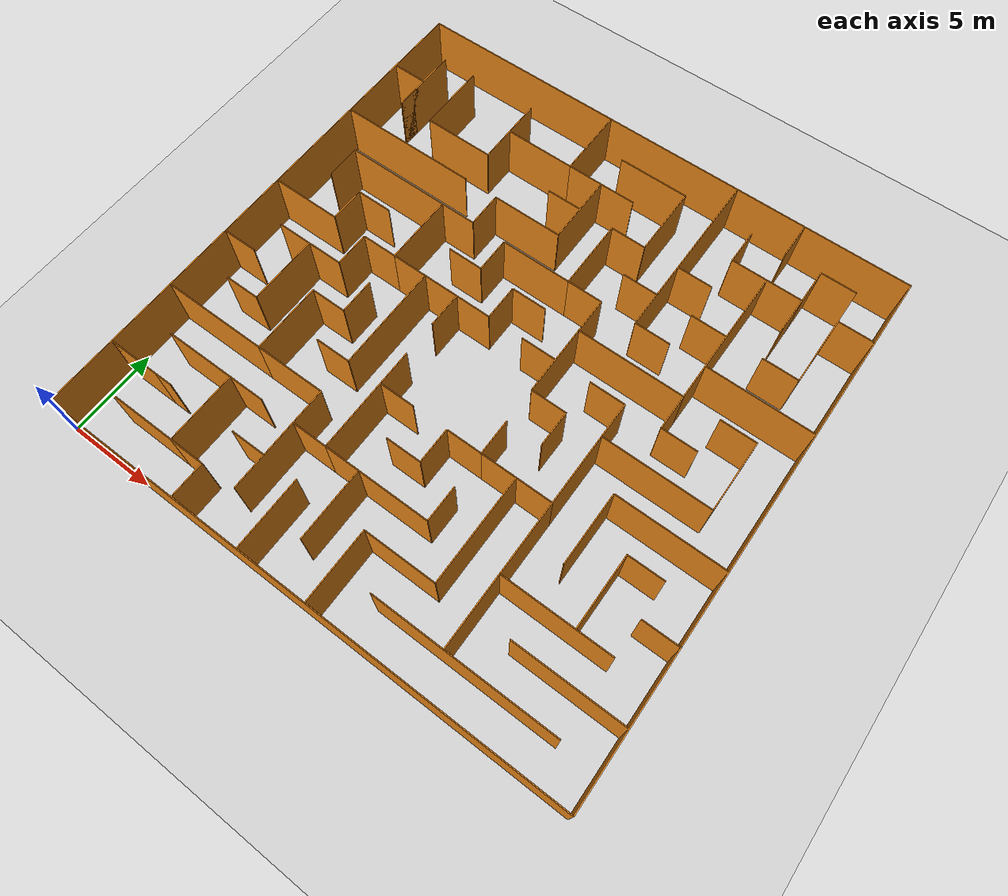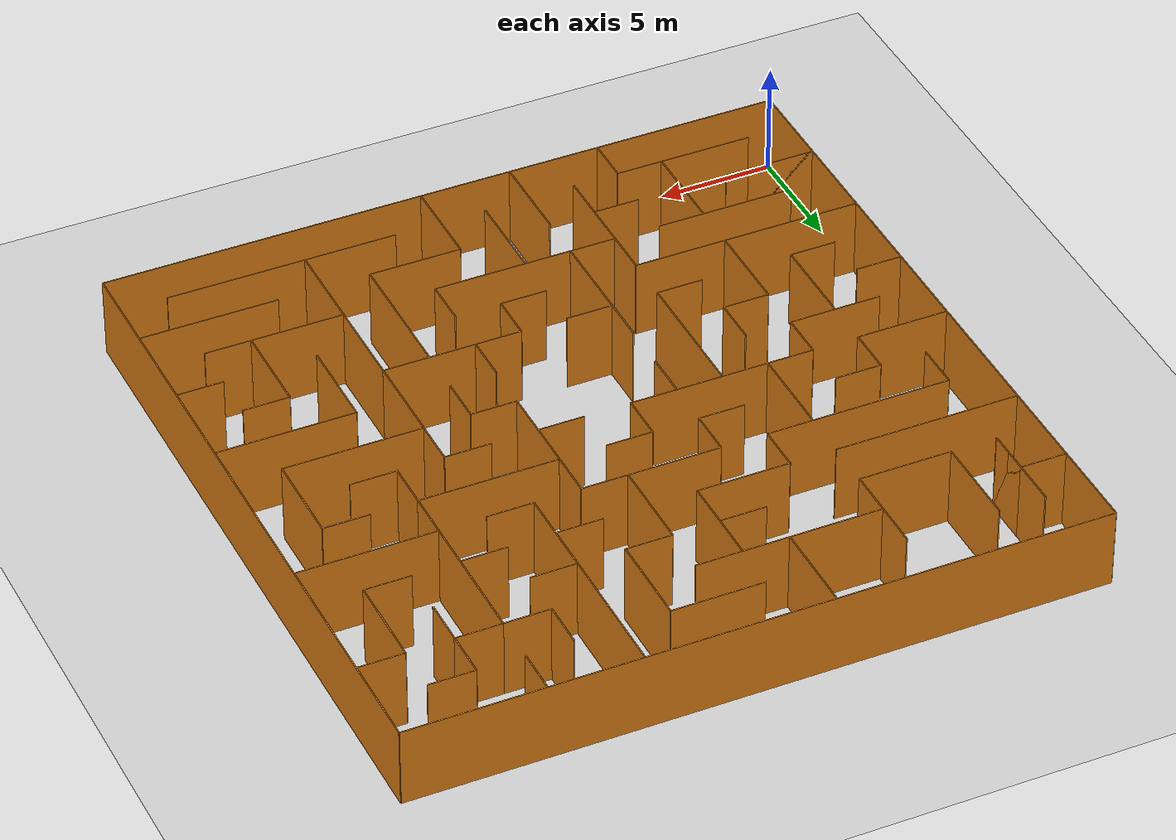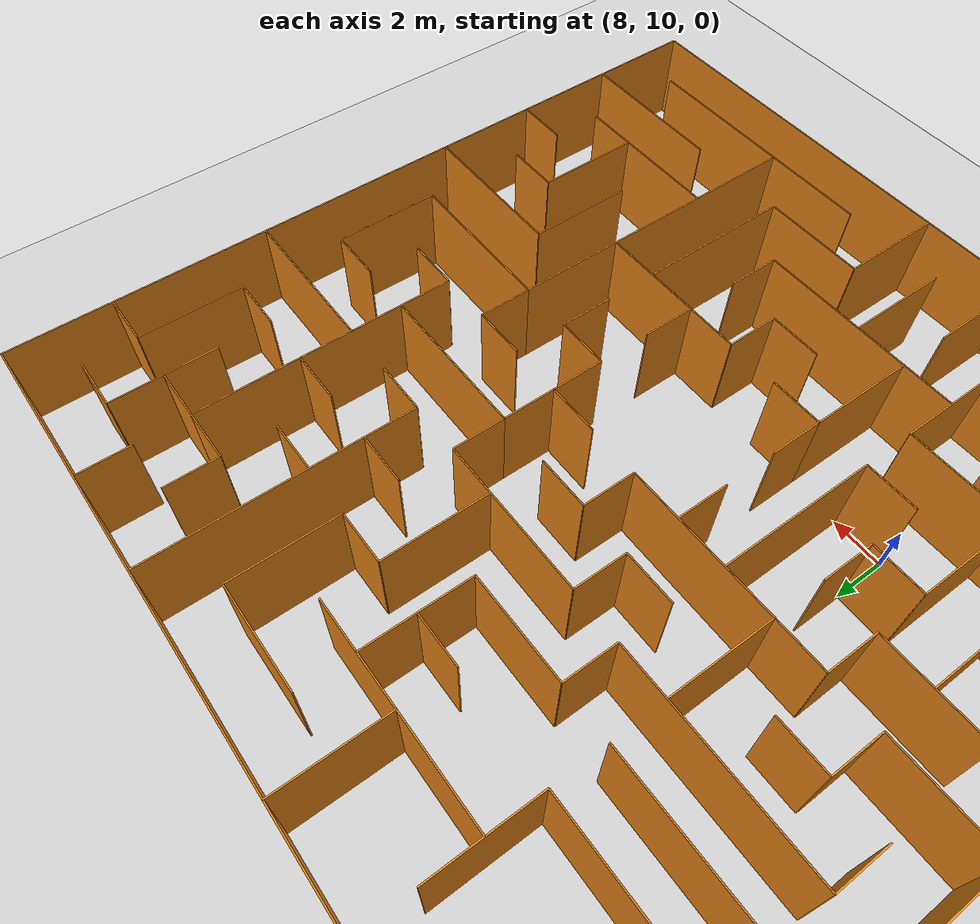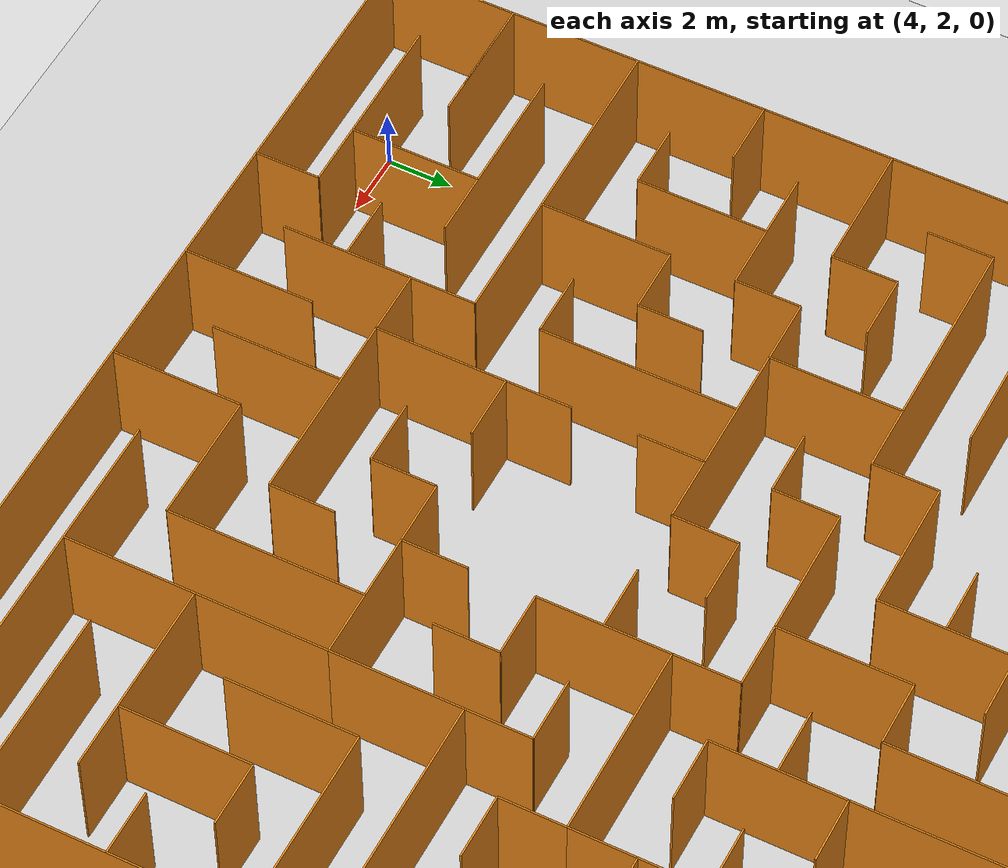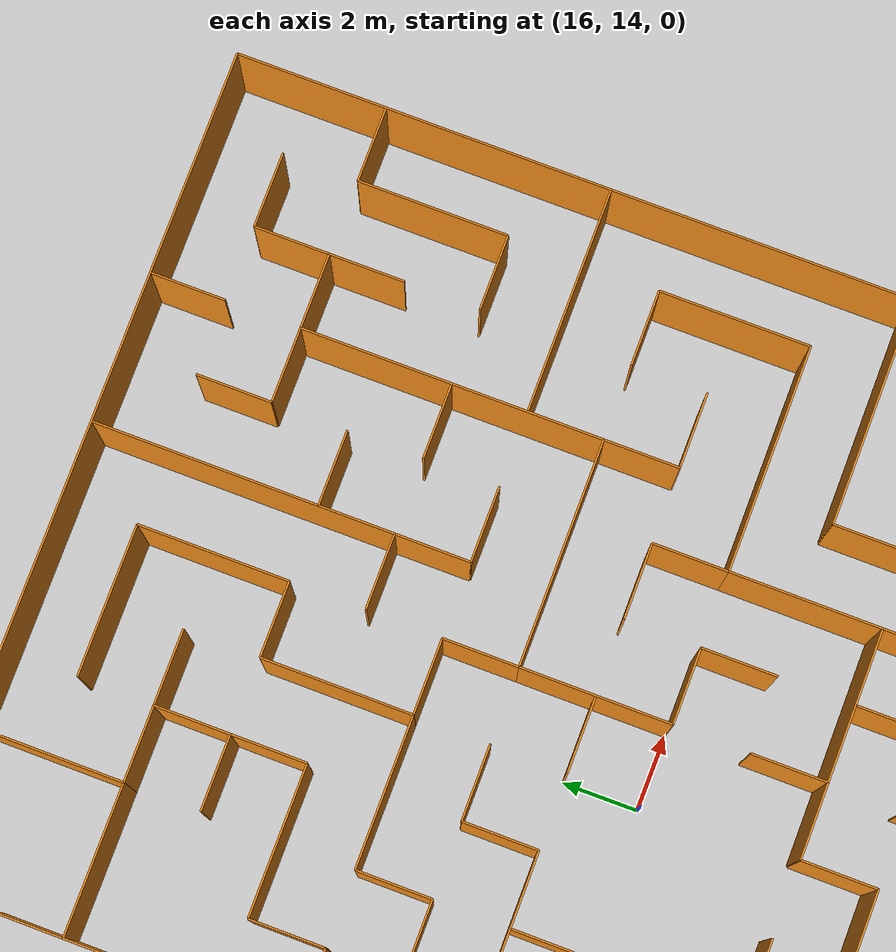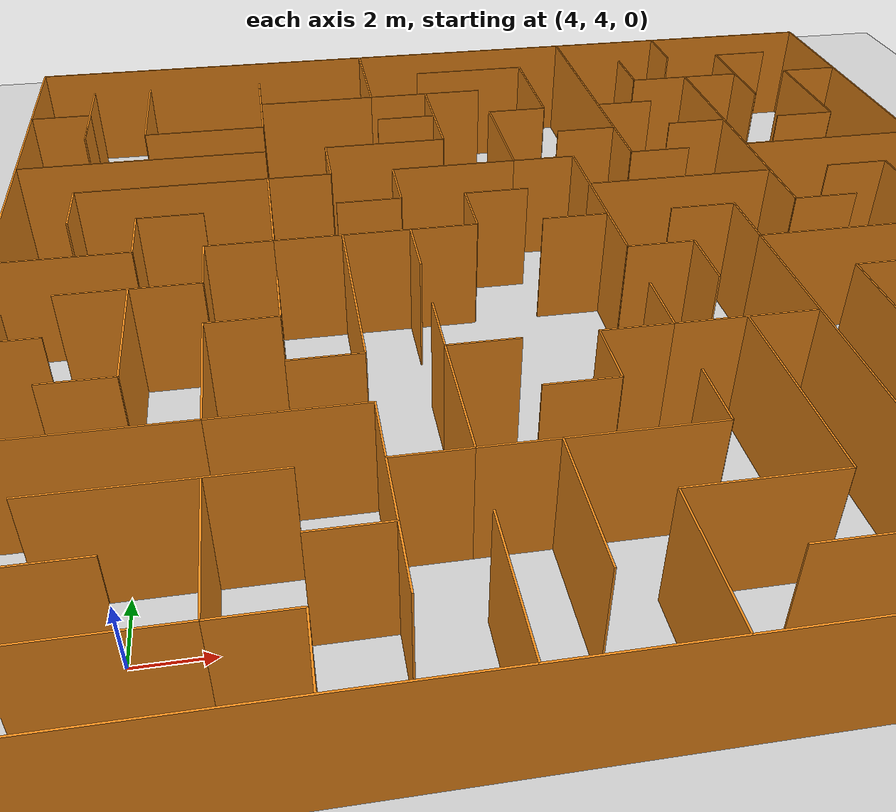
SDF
<sdf version="1.6">
  <world name="default">
    <model name="box_115">
  <pose frame="">27.0 12.0 1.75 0 0 -3.141592653589793</pose>
  <link name="link">
    <inertial>
      <mass>1</mass>
      <inertia>
        <ixx>0</ixx>
        <ixy>0</ixy>
        <ixz>0</ixz>
        <iyy>0</iyy>
        <iyz>0</iyz>
        <izz>0</izz>
      </inertia>
    </inertial>
    <collision name="collision">
      <geometry>
        <box>
          <size>6.0 0.05 3.5</size>
        </box>
      </geometry>
      <max_contacts>10</max_contacts>
      <surface>
        <contact>
          <ode/>
        </contact>
        <bounce/>
        <friction>
          <torsional>
            <ode/>
          </torsional>
          <ode/>
        </friction>
      </surface>
    </collision>
    <visual name="visual">
      <geometry>
        <box>
          <size>6.0 0.05 3.5</size>
        </box>
      </geometry>
      <material>
        <script>
          <name>Gazebo/Orange</name>
          <uri>file://media/materials/scripts/gazebo.material</uri>
        </script>
      </material>
    </visual>
    <self_collide>0</self_collide>
    <enable_wind>0</enable_wind>
    <kinematic>0</kinematic>
  </link>
	<static>1</static>
</model><model name="box_114">
  <pose frame="">24.0 10.0 1.75 0 0 -1.5707963267948966</pose>
  <link name="link">
    <inertial>
      <mass>1</mass>
      <inertia>
        <ixx>0</ixx>
        <ixy>0</ixy>
        <ixz>0</ixz>
        <iyy>0</iyy>
        <iyz>0</iyz>
        <izz>0</izz>
      </inertia>
    </inertial>
    <collision name="collision">
      <geometry>
        <box>
          <size>4.0 0.05 3.5</size>
        </box>
      </geometry>
      <max_contacts>10</max_contacts>
      <surface>
        <contact>
          <ode/>
        </contact>
        <bounce/>
        <friction>
          <torsional>
            <ode/>
          </torsional>
          <ode/>
        </friction>
      </surface>
    </collision>
    <visual name="visual">
      <geometry>
        <box>
          <size>4.0 0.05 3.5</size>
        </box>
      </geometry>
      <material>
        <script>
          <name>Gazebo/Orange</name>
          <uri>file://media/materials/scripts/gazebo.material</uri>
        </script>
      </material>
    </visual>
    <self_collide>0</self_collide>
    <enable_wind>0</enable_wind>
    <kinematic>0</kinematic>
  </link>
	<static>1</static>
</model><model name="box_113">
  <pose frame="">27.0 10.0 1.75 0 0 -3.141592653589793</pose>
  <link name="link">
    <inertial>
      <mass>1</mass>
      <inertia>
        <ixx>0</ixx>
        <ixy>0</ixy>
        <ixz>0</ixz>
        <iyy>0</iyy>
        <iyz>0</iyz>
        <izz>0</izz>
      </inertia>
    </inertial>
    <collision name="collision">
      <geometry>
        <box>
          <size>2.0 0.05 3.5</size>
        </box>
      </geometry>
      <max_contacts>10</max_contacts>
      <surface>
        <contact>
          <ode/>
        </contact>
        <bounce/>
        <friction>
          <torsional>
            <ode/>
          </torsional>
          <ode/>
        </friction>
      </surface>
    </collision>
    <visual name="visual">
      <geometry>
        <box>
          <size>2.0 0.05 3.5</size>
        </box>
      </geometry>
      <material>
        <script>
          <name>Gazebo/Orange</name>
          <uri>file://media/materials/scripts/gazebo.material</uri>
        </script>
      </material>
    </visual>
    <self_collide>0</self_collide>
    <enable_wind>0</enable_wind>
    <kinematic>0</kinematic>
  </link>
	<static>1</static>
</model><model name="box_112">
  <pose frame="">26.0 8.0 1.75 0 0 -1.5707963267948966</pose>
  <link name="link">
    <inertial>
      <mass>1</mass>
      <inertia>
        <ixx>0</ixx>
        <ixy>0</ixy>
        <ixz>0</ixz>
        <iyy>0</iyy>
        <iyz>0</iyz>
        <izz>0</izz>
      </inertia>
    </inertial>
    <collision name="collision">
      <geometry>
        <box>
          <size>4.0 0.05 3.5</size>
        </box>
      </geometry>
      <max_contacts>10</max_contacts>
      <surface>
        <contact>
          <ode/>
        </contact>
        <bounce/>
        <friction>
          <torsional>
            <ode/>
          </torsional>
          <ode/>
        </friction>
      </surface>
    </collision>
    <visual name="visual">
      <geometry>
        <box>
          <size>4.0 0.05 3.5</size>
        </box>
      </geometry>
      <material>
        <script>
          <name>Gazebo/Orange</name>
          <uri>file://media/materials/scripts/gazebo.material</uri>
        </script>
      </material>
    </visual>
    <self_collide>0</self_collide>
    <enable_wind>0</enable_wind>
    <kinematic>0</kinematic>
  </link>
	<static>1</static>
</model><model name="box_111">
  <pose frame="">29.0 8.0 1.75 0 0 -0.0</pose>
  <link name="link">
    <inertial>
      <mass>1</mass>
      <inertia>
        <ixx>0</ixx>
        <ixy>0</ixy>
        <ixz>0</ixz>
        <iyy>0</iyy>
        <iyz>0</iyz>
        <izz>0</izz>
      </inertia>
    </inertial>
    <collision name="collision">
      <geometry>
        <box>
          <size>2.0 0.05 3.5</size>
        </box>
      </geometry>
      <max_contacts>10</max_contacts>
      <surface>
        <contact>
          <ode/>
        </contact>
        <bounce/>
        <friction>
          <torsional>
            <ode/>
          </torsional>
          <ode/>
        </friction>
      </surface>
    </collision>
    <visual name="visual">
      <geometry>
        <box>
          <size>2.0 0.05 3.5</size>
        </box>
      </geometry>
      <material>
        <script>
          <name>Gazebo/Orange</name>
          <uri>file://media/materials/scripts/gazebo.material</uri>
        </script>
      </material>
    </visual>
    <self_collide>0</self_collide>
    <enable_wind>0</enable_wind>
    <kinematic>0</kinematic>
  </link>
	<static>1</static>
</model><model name="box_110">
  <pose frame="">27.0 4.0 1.75 0 0 -0.0</pose>
  <link name="link">
    <inertial>
      <mass>1</mass>
      <inertia>
        <ixx>0</ixx>
        <ixy>0</ixy>
        <ixz>0</ixz>
        <iyy>0</iyy>
        <iyz>0</iyz>
        <izz>0</izz>
      </inertia>
    </inertial>
    <collision name="collision">
      <geometry>
        <box>
          <size>6.0 0.05 3.5</size>
        </box>
      </geometry>
      <max_contacts>10</max_contacts>
      <surface>
        <contact>
          <ode/>
        </contact>
        <bounce/>
        <friction>
          <torsional>
            <ode/>
          </torsional>
          <ode/>
        </friction>
      </surface>
    </collision>
    <visual name="visual">
      <geometry>
        <box>
          <size>6.0 0.05 3.5</size>
        </box>
      </geometry>
      <material>
        <script>
          <name>Gazebo/Orange</name>
          <uri>file://media/materials/scripts/gazebo.material</uri>
        </script>
      </material>
    </visual>
    <self_collide>0</self_collide>
    <enable_wind>0</enable_wind>
    <kinematic>0</kinematic>
  </link>
	<static>1</static>
</model><model name="box_109">
  <pose frame="">25.0 6.0 1.75 0 0 -3.141592653589793</pose>
  <link name="link">
    <inertial>
      <mass>1</mass>
      <inertia>
        <ixx>0</ixx>
        <ixy>0</ixy>
        <ixz>0</ixz>
        <iyy>0</iyy>
        <iyz>0</iyz>
        <izz>0</izz>
      </inertia>
    </inertial>
    <collision name="collision">
      <geometry>
        <box>
          <size>6.0 0.05 3.5</size>
        </box>
      </geometry>
      <max_contacts>10</max_contacts>
      <surface>
        <contact>
          <ode/>
        </contact>
        <bounce/>
        <friction>
          <torsional>
            <ode/>
          </torsional>
          <ode/>
        </friction>
      </surface>
    </collision>
    <visual name="visual">
      <geometry>
        <box>
          <size>6.0 0.05 3.5</size>
        </box>
      </geometry>
      <material>
        <script>
          <name>Gazebo/Orange</name>
          <uri>file://media/materials/scripts/gazebo.material</uri>
        </script>
      </material>
    </visual>
    <self_collide>0</self_collide>
    <enable_wind>0</enable_wind>
    <kinematic>0</kinematic>
  </link>
	<static>1</static>
</model><model name="box_108">
  <pose frame="">22.0 6.0 1.75 0 0 1.5707963267948966</pose>
  <link name="link">
    <inertial>
      <mass>1</mass>
      <inertia>
        <ixx>0</ixx>
        <ixy>0</ixy>
        <ixz>0</ixz>
        <iyy>0</iyy>
        <iyz>0</iyz>
        <izz>0</izz>
      </inertia>
    </inertial>
    <collision name="collision">
      <geometry>
        <box>
          <size>8.0 0.05 3.5</size>
        </box>
      </geometry>
      <max_contacts>10</max_contacts>
      <surface>
        <contact>
          <ode/>
        </contact>
        <bounce/>
        <friction>
          <torsional>
            <ode/>
          </torsional>
          <ode/>
        </friction>
      </surface>
    </collision>
    <visual name="visual">
      <geometry>
        <box>
          <size>8.0 0.05 3.5</size>
        </box>
      </geometry>
      <material>
        <script>
          <name>Gazebo/Orange</name>
          <uri>file://media/materials/scripts/gazebo.material</uri>
        </script>
      </material>
    </visual>
    <self_collide>0</self_collide>
    <enable_wind>0</enable_wind>
    <kinematic>0</kinematic>
  </link>
	<static>1</static>
</model><model name="box_107">
  <pose frame="">23.0 2.0 1.75 0 0 -3.141592653589793</pose>
  <link name="link">
    <inertial>
      <mass>1</mass>
      <inertia>
        <ixx>0</ixx>
        <ixy>0</ixy>
        <ixz>0</ixz>
        <iyy>0</iyy>
        <iyz>0</iyz>
        <izz>0</izz>
      </inertia>
    </inertial>
    <collision name="collision">
      <geometry>
        <box>
          <size>10.0 0.05 3.5</size>
        </box>
      </geometry>
      <max_contacts>10</max_contacts>
      <surface>
        <contact>
          <ode/>
        </contact>
        <bounce/>
        <friction>
          <torsional>
            <ode/>
          </torsional>
          <ode/>
        </friction>
      </surface>
    </collision>
    <visual name="visual">
      <geometry>
        <box>
          <size>10.0 0.05 3.5</size>
        </box>
      </geometry>
      <material>
        <script>
          <name>Gazebo/Orange</name>
          <uri>file://media/materials/scripts/gazebo.material</uri>
        </script>
      </material>
    </visual>
    <self_collide>0</self_collide>
    <enable_wind>0</enable_wind>
    <kinematic>0</kinematic>
  </link>
	<static>1</static>
</model><model name="box_106">
  <pose frame="">20.0 7.0 1.75 0 0 -1.5707963267948966</pose>
  <link name="link">
    <inertial>
      <mass>1</mass>
      <inertia>
        <ixx>0</ixx>
        <ixy>0</ixy>
        <ixz>0</ixz>
        <iyy>0</iyy>
        <iyz>0</iyz>
        <izz>0</izz>
      </inertia>
    </inertial>
    <collision name="collision">
      <geometry>
        <box>
          <size>6.0 0.05 3.5</size>
        </box>
      </geometry>
      <max_contacts>10</max_contacts>
      <surface>
        <contact>
          <ode/>
        </contact>
        <bounce/>
        <friction>
          <torsional>
            <ode/>
          </torsional>
          <ode/>
        </friction>
      </surface>
    </collision>
    <visual name="visual">
      <geometry>
        <box>
          <size>6.0 0.05 3.5</size>
        </box>
      </geometry>
      <material>
        <script>
          <name>Gazebo/Orange</name>
          <uri>file://media/materials/scripts/gazebo.material</uri>
        </script>
      </material>
    </visual>
    <self_collide>0</self_collide>
    <enable_wind>0</enable_wind>
    <kinematic>0</kinematic>
  </link>
	<static>1</static>
</model><model name="box_105">
  <pose frame="">18.0 4.0 1.75 0 0 -3.141592653589793</pose>
  <link name="link">
    <inertial>
      <mass>1</mass>
      <inertia>
        <ixx>0</ixx>
        <ixy>0</ixy>
        <ixz>0</ixz>
        <iyy>0</iyy>
        <iyz>0</iyz>
        <izz>0</izz>
      </inertia>
    </inertial>
    <collision name="collision">
      <geometry>
        <box>
          <size>4.0 0.05 3.5</size>
        </box>
      </geometry>
      <max_contacts>10</max_contacts>
      <surface>
        <contact>
          <ode/>
        </contact>
        <bounce/>
        <friction>
          <torsional>
            <ode/>
          </torsional>
          <ode/>
        </friction>
      </surface>
    </collision>
    <visual name="visual">
      <geometry>
        <box>
          <size>4.0 0.05 3.5</size>
        </box>
      </geometry>
      <material>
        <script>
          <name>Gazebo/Orange</name>
          <uri>file://media/materials/scripts/gazebo.material</uri>
        </script>
      </material>
    </visual>
    <self_collide>0</self_collide>
    <enable_wind>0</enable_wind>
    <kinematic>0</kinematic>
  </link>
	<static>1</static>
</model><model name="box_104">
  <pose frame="">16.0 2.0 1.75 0 0 -1.5707963267948966</pose>
  <link name="link">
    <inertial>
      <mass>1</mass>
      <inertia>
        <ixx>0</ixx>
        <ixy>0</ixy>
        <ixz>0</ixz>
        <iyy>0</iyy>
        <iyz>0</iyz>
        <izz>0</izz>
      </inertia>
    </inertial>
    <collision name="collision">
      <geometry>
        <box>
          <size>4.0 0.05 3.5</size>
        </box>
      </geometry>
      <max_contacts>10</max_contacts>
      <surface>
        <contact>
          <ode/>
        </contact>
        <bounce/>
        <friction>
          <torsional>
            <ode/>
          </torsional>
          <ode/>
        </friction>
      </surface>
    </collision>
    <visual name="visual">
      <geometry>
        <box>
          <size>4.0 0.05 3.5</size>
        </box>
      </geometry>
      <material>
        <script>
          <name>Gazebo/Orange</name>
          <uri>file://media/materials/scripts/gazebo.material</uri>
        </script>
      </material>
    </visual>
    <self_collide>0</self_collide>
    <enable_wind>0</enable_wind>
    <kinematic>0</kinematic>
  </link>
	<static>1</static>
</model><model name="box_103">
  <pose frame="">12.0 2.0 1.75 0 0 1.5707963267948966</pose>
  <link name="link">
    <inertial>
      <mass>1</mass>
      <inertia>
        <ixx>0</ixx>
        <ixy>0</ixy>
        <ixz>0</ixz>
        <iyy>0</iyy>
        <iyz>0</iyz>
        <izz>0</izz>
      </inertia>
    </inertial>
    <collision name="collision">
      <geometry>
        <box>
          <size>4.0 0.05 3.5</size>
        </box>
      </geometry>
      <max_contacts>10</max_contacts>
      <surface>
        <contact>
          <ode/>
        </contact>
        <bounce/>
        <friction>
          <torsional>
            <ode/>
          </torsional>
          <ode/>
        </friction>
      </surface>
    </collision>
    <visual name="visual">
      <geometry>
        <box>
          <size>4.0 0.05 3.5</size>
        </box>
      </geometry>
      <material>
        <script>
          <name>Gazebo/Orange</name>
          <uri>file://media/materials/scripts/gazebo.material</uri>
        </script>
      </material>
    </visual>
    <self_collide>0</self_collide>
    <enable_wind>0</enable_wind>
    <kinematic>0</kinematic>
  </link>
	<static>1</static>
</model><model name="box_102">
  <pose frame="">2.0 4.0 1.75 0 0 -3.141592653589793</pose>
  <link name="link">
    <inertial>
      <mass>1</mass>
      <inertia>
        <ixx>0</ixx>
        <ixy>0</ixy>
        <ixz>0</ixz>
        <iyy>0</iyy>
        <iyz>0</iyz>
        <izz>0</izz>
      </inertia>
    </inertial>
    <collision name="collision">
      <geometry>
        <box>
          <size>4.0 0.05 3.5</size>
        </box>
      </geometry>
      <max_contacts>10</max_contacts>
      <surface>
        <contact>
          <ode/>
        </contact>
        <bounce/>
        <friction>
          <torsional>
            <ode/>
          </torsional>
          <ode/>
        </friction>
      </surface>
    </collision>
    <visual name="visual">
      <geometry>
        <box>
          <size>4.0 0.05 3.5</size>
        </box>
      </geometry>
      <material>
        <script>
          <name>Gazebo/Orange</name>
          <uri>file://media/materials/scripts/gazebo.material</uri>
        </script>
      </material>
    </visual>
    <self_collide>0</self_collide>
    <enable_wind>0</enable_wind>
    <kinematic>0</kinematic>
  </link>
	<static>1</static>
</model><model name="box_101">
  <pose frame="">1.5 4.0 1.75 0 0 -0.0</pose>
  <link name="link">
    <inertial>
      <mass>1</mass>
      <inertia>
        <ixx>0</ixx>
        <ixy>0</ixy>
        <ixz>0</ixz>
        <iyy>0</iyy>
        <iyz>0</iyz>
        <izz>0</izz>
      </inertia>
    </inertial>
    <collision name="collision">
      <geometry>
        <box>
          <size>3.0 0.05 3.5</size>
        </box>
      </geometry>
      <max_contacts>10</max_contacts>
      <surface>
        <contact>
          <ode/>
        </contact>
        <bounce/>
        <friction>
          <torsional>
            <ode/>
          </torsional>
          <ode/>
        </friction>
      </surface>
    </collision>
    <visual name="visual">
      <geometry>
        <box>
          <size>3.0 0.05 3.5</size>
        </box>
      </geometry>
      <material>
        <script>
          <name>Gazebo/Orange</name>
          <uri>file://media/materials/scripts/gazebo.material</uri>
        </script>
      </material>
    </visual>
    <self_collide>0</self_collide>
    <enable_wind>0</enable_wind>
    <kinematic>0</kinematic>
  </link>
	<static>1</static>
</model><model name="box_100">
  <pose frame="">4.0 2.0 1.75 0 0 -0.0</pose>
  <link name="link">
    <inertial>
      <mass>1</mass>
      <inertia>
        <ixx>0</ixx>
        <ixy>0</ixy>
        <ixz>0</ixz>
        <iyy>0</iyy>
        <iyz>0</iyz>
        <izz>0</izz>
      </inertia>
    </inertial>
    <collision name="collision">
      <geometry>
        <box>
          <size>4.0 0.05 3.5</size>
        </box>
      </geometry>
      <max_contacts>10</max_contacts>
      <surface>
        <contact>
          <ode/>
        </contact>
        <bounce/>
        <friction>
          <torsional>
            <ode/>
          </torsional>
          <ode/>
        </friction>
      </surface>
    </collision>
    <visual name="visual">
      <geometry>
        <box>
          <size>4.0 0.05 3.5</size>
        </box>
      </geometry>
      <material>
        <script>
          <name>Gazebo/Orange</name>
          <uri>file://media/materials/scripts/gazebo.material</uri>
        </script>
      </material>
    </visual>
    <self_collide>0</self_collide>
    <enable_wind>0</enable_wind>
    <kinematic>0</kinematic>
  </link>
	<static>1</static>
</model><model name="box_99">
  <pose frame="">8.0 1.0 1.75 0 0 1.5707963267948966</pose>
  <link name="link">
    <inertial>
      <mass>1</mass>
      <inertia>
        <ixx>0</ixx>
        <ixy>0</ixy>
        <ixz>0</ixz>
        <iyy>0</iyy>
        <iyz>0</iyz>
        <izz>0</izz>
      </inertia>
    </inertial>
    <collision name="collision">
      <geometry>
        <box>
          <size>2.0 0.05 3.5</size>
        </box>
      </geometry>
      <max_contacts>10</max_contacts>
      <surface>
        <contact>
          <ode/>
        </contact>
        <bounce/>
        <friction>
          <torsional>
            <ode/>
          </torsional>
          <ode/>
        </friction>
      </surface>
    </collision>
    <visual name="visual">
      <geometry>
        <box>
          <size>2.0 0.05 3.5</size>
        </box>
      </geometry>
      <material>
        <script>
          <name>Gazebo/Orange</name>
          <uri>file://media/materials/scripts/gazebo.material</uri>
        </script>
      </material>
    </visual>
    <self_collide>0</self_collide>
    <enable_wind>0</enable_wind>
    <kinematic>0</kinematic>
  </link>
	<static>1</static>
</model><model name="box_98">
  <pose frame="">7.0 2.0 1.75 0 0 -3.141592653589793</pose>
  <link name="link">
    <inertial>
      <mass>1</mass>
      <inertia>
        <ixx>0</ixx>
        <ixy>0</ixy>
        <ixz>0</ixz>
        <iyy>0</iyy>
        <iyz>0</iyz>
        <izz>0</izz>
      </inertia>
    </inertial>
    <collision name="collision">
      <geometry>
        <box>
          <size>2.0 0.05 3.5</size>
        </box>
      </geometry>
      <max_contacts>10</max_contacts>
      <surface>
        <contact>
          <ode/>
        </contact>
        <bounce/>
        <friction>
          <torsional>
            <ode/>
          </torsional>
          <ode/>
        </friction>
      </surface>
    </collision>
    <visual name="visual">
      <geometry>
        <box>
          <size>2.0 0.05 3.5</size>
        </box>
      </geometry>
      <material>
        <script>
          <name>Gazebo/Orange</name>
          <uri>file://media/materials/scripts/gazebo.material</uri>
        </script>
      </material>
    </visual>
    <self_collide>0</self_collide>
    <enable_wind>0</enable_wind>
    <kinematic>0</kinematic>
  </link>
	<static>1</static>
</model><model name="box_97">
  <pose frame="">6.0 4.0 1.75 0 0 1.5707963267948966</pose>
  <link name="link">
    <inertial>
      <mass>1</mass>
      <inertia>
        <ixx>0</ixx>
        <ixy>0</ixy>
        <ixz>0</ixz>
        <iyy>0</iyy>
        <iyz>0</iyz>
        <izz>0</izz>
      </inertia>
    </inertial>
    <collision name="collision">
      <geometry>
        <box>
          <size>4.0 0.05 3.5</size>
        </box>
      </geometry>
      <max_contacts>10</max_contacts>
      <surface>
        <contact>
          <ode/>
        </contact>
        <bounce/>
        <friction>
          <torsional>
            <ode/>
          </torsional>
          <ode/>
        </friction>
      </surface>
    </collision>
    <visual name="visual">
      <geometry>
        <box>
          <size>4.0 0.05 3.5</size>
        </box>
      </geometry>
      <material>
        <script>
          <name>Gazebo/Orange</name>
          <uri>file://media/materials/scripts/gazebo.material</uri>
        </script>
      </material>
    </visual>
    <self_collide>0</self_collide>
    <enable_wind>0</enable_wind>
    <kinematic>0</kinematic>
  </link>
	<static>1</static>
</model><model name="box_96">
  <pose frame="">5.0 6.0 1.75 0 0 -0.0</pose>
  <link name="link">
    <inertial>
      <mass>1</mass>
      <inertia>
        <ixx>0</ixx>
        <ixy>0</ixy>
        <ixz>0</ixz>
        <iyy>0</iyy>
        <iyz>0</iyz>
        <izz>0</izz>
      </inertia>
    </inertial>
    <collision name="collision">
      <geometry>
        <box>
          <size>6.0 0.05 3.5</size>
        </box>
      </geometry>
      <max_contacts>10</max_contacts>
      <surface>
        <contact>
          <ode/>
        </contact>
        <bounce/>
        <friction>
          <torsional>
            <ode/>
          </torsional>
          <ode/>
        </friction>
      </surface>
    </collision>
    <visual name="visual">
      <geometry>
        <box>
          <size>6.0 0.05 3.5</size>
        </box>
      </geometry>
      <material>
        <script>
          <name>Gazebo/Orange</name>
          <uri>file://media/materials/scripts/gazebo.material</uri>
        </script>
      </material>
    </visual>
    <self_collide>0</self_collide>
    <enable_wind>0</enable_wind>
    <kinematic>0</kinematic>
  </link>
	<static>1</static>
</model><model name="box_95">
  <pose frame="">3.0 8.0 1.75 0 0 -0.0</pose>
  <link name="link">
    <inertial>
      <mass>1</mass>
      <inertia>
        <ixx>0</ixx>
        <ixy>0</ixy>
        <ixz>0</ixz>
        <iyy>0</iyy>
        <iyz>0</iyz>
        <izz>0</izz>
      </inertia>
    </inertial>
    <collision name="collision">
      <geometry>
        <box>
          <size>6.0 0.05 3.5</size>
        </box>
      </geometry>
      <max_contacts>10</max_contacts>
      <surface>
        <contact>
          <ode/>
        </contact>
        <bounce/>
        <friction>
          <torsional>
            <ode/>
          </torsional>
          <ode/>
        </friction>
      </surface>
    </collision>
    <visual name="visual">
      <geometry>
        <box>
          <size>6.0 0.05 3.5</size>
        </box>
      </geometry>
      <material>
        <script>
          <name>Gazebo/Orange</name>
          <uri>file://media/materials/scripts/gazebo.material</uri>
        </script>
      </material>
    </visual>
    <self_collide>0</self_collide>
    <enable_wind>0</enable_wind>
    <kinematic>0</kinematic>
  </link>
	<static>1</static>
</model><model name="box_94">
  <pose frame="">17.0 16.0 1.75 0 0 -0.0</pose>
  <link name="link">
    <inertial>
      <mass>1</mass>
      <inertia>
        <ixx>0</ixx>
        <ixy>0</ixy>
        <ixz>0</ixz>
        <iyy>0</iyy>
        <iyz>0</iyz>
        <izz>0</izz>
      </inertia>
    </inertial>
    <collision name="collision">
      <geometry>
        <box>
          <size>2.0 0.05 3.5</size>
        </box>
      </geometry>
      <max_contacts>10</max_contacts>
      <surface>
        <contact>
          <ode/>
        </contact>
        <bounce/>
        <friction>
          <torsional>
            <ode/>
          </torsional>
          <ode/>
        </friction>
      </surface>
    </collision>
    <visual name="visual">
      <geometry>
        <box>
          <size>2.0 0.05 3.5</size>
        </box>
      </geometry>
      <material>
        <script>
          <name>Gazebo/Orange</name>
          <uri>file://media/materials/scripts/gazebo.material</uri>
        </script>
      </material>
    </visual>
    <self_collide>0</self_collide>
    <enable_wind>0</enable_wind>
    <kinematic>0</kinematic>
  </link>
	<static>1</static>
</model><model name="box_93">
  <pose frame="">11.0 6.0 1.75 0 0 -0.0</pose>
  <link name="link">
    <inertial>
      <mass>1</mass>
      <inertia>
        <ixx>0</ixx>
        <ixy>0</ixy>
        <ixz>0</ixz>
        <iyy>0</iyy>
        <iyz>0</iyz>
        <izz>0</izz>
      </inertia>
    </inertial>
    <collision name="collision">
      <geometry>
        <box>
          <size>2.0 0.05 3.5</size>
        </box>
      </geometry>
      <max_contacts>10</max_contacts>
      <surface>
        <contact>
          <ode/>
        </contact>
        <bounce/>
        <friction>
          <torsional>
            <ode/>
          </torsional>
          <ode/>
        </friction>
      </surface>
    </collision>
    <visual name="visual">
      <geometry>
        <box>
          <size>2.0 0.05 3.5</size>
        </box>
      </geometry>
      <material>
        <script>
          <name>Gazebo/Orange</name>
          <uri>file://media/materials/scripts/gazebo.material</uri>
        </script>
      </material>
    </visual>
    <self_collide>0</self_collide>
    <enable_wind>0</enable_wind>
    <kinematic>0</kinematic>
  </link>
	<static>1</static>
</model><model name="box_92">
  <pose frame="">9.0 4.0 1.75 0 0 -0.0</pose>
  <link name="link">
    <inertial>
      <mass>1</mass>
      <inertia>
        <ixx>0</ixx>
        <ixy>0</ixy>
        <ixz>0</ixz>
        <iyy>0</iyy>
        <iyz>0</iyz>
        <izz>0</izz>
      </inertia>
    </inertial>
    <collision name="collision">
      <geometry>
        <box>
          <size>2.0 0.05 3.5</size>
        </box>
      </geometry>
      <max_contacts>10</max_contacts>
      <surface>
        <contact>
          <ode/>
        </contact>
        <bounce/>
        <friction>
          <torsional>
            <ode/>
          </torsional>
          <ode/>
        </friction>
      </surface>
    </collision>
    <visual name="visual">
      <geometry>
        <box>
          <size>2.0 0.05 3.5</size>
        </box>
      </geometry>
      <material>
        <script>
          <name>Gazebo/Orange</name>
          <uri>file://media/materials/scripts/gazebo.material</uri>
        </script>
      </material>
    </visual>
    <self_collide>0</self_collide>
    <enable_wind>0</enable_wind>
    <kinematic>0</kinematic>
  </link>
	<static>1</static>
</model><model name="box_91">
  <pose frame="">10.0 5.0 1.75 0 0 1.5707963267948966</pose>
  <link name="link">
    <inertial>
      <mass>1</mass>
      <inertia>
        <ixx>0</ixx>
        <ixy>0</ixy>
        <ixz>0</ixz>
        <iyy>0</iyy>
        <iyz>0</iyz>
        <izz>0</izz>
      </inertia>
    </inertial>
    <collision name="collision">
      <geometry>
        <box>
          <size>6.0 0.05 3.5</size>
        </box>
      </geometry>
      <max_contacts>10</max_contacts>
      <surface>
        <contact>
          <ode/>
        </contact>
        <bounce/>
        <friction>
          <torsional>
            <ode/>
          </torsional>
          <ode/>
        </friction>
      </surface>
    </collision>
    <visual name="visual">
      <geometry>
        <box>
          <size>6.0 0.05 3.5</size>
        </box>
      </geometry>
      <material>
        <script>
          <name>Gazebo/Orange</name>
          <uri>file://media/materials/scripts/gazebo.material</uri>
        </script>
      </material>
    </visual>
    <self_collide>0</self_collide>
    <enable_wind>0</enable_wind>
    <kinematic>0</kinematic>
  </link>
	<static>1</static>
</model><model name="box_90">
  <pose frame="">8.0 8.0 1.75 0 0 -3.141592653589793</pose>
  <link name="link">
    <inertial>
      <mass>1</mass>
      <inertia>
        <ixx>0</ixx>
        <ixy>0</ixy>
        <ixz>0</ixz>
        <iyy>0</iyy>
        <iyz>0</iyz>
        <izz>0</izz>
      </inertia>
    </inertial>
    <collision name="collision">
      <geometry>
        <box>
          <size>4.0 0.05 3.5</size>
        </box>
      </geometry>
      <max_contacts>10</max_contacts>
      <surface>
        <contact>
          <ode/>
        </contact>
        <bounce/>
        <friction>
          <torsional>
            <ode/>
          </torsional>
          <ode/>
        </friction>
      </surface>
    </collision>
    <visual name="visual">
      <geometry>
        <box>
          <size>4.0 0.05 3.5</size>
        </box>
      </geometry>
      <material>
        <script>
          <name>Gazebo/Orange</name>
          <uri>file://media/materials/scripts/gazebo.material</uri>
        </script>
      </material>
    </visual>
    <self_collide>0</self_collide>
    <enable_wind>0</enable_wind>
    <kinematic>0</kinematic>
  </link>
	<static>1</static>
</model><model name="box_89">
  <pose frame="">6.0 10.0 1.75 0 0 1.5707963267948966</pose>
  <link name="link">
    <inertial>
      <mass>1</mass>
      <inertia>
        <ixx>0</ixx>
        <ixy>0</ixy>
        <ixz>0</ixz>
        <iyy>0</iyy>
        <iyz>0</iyz>
        <izz>0</izz>
      </inertia>
    </inertial>
    <collision name="collision">
      <geometry>
        <box>
          <size>4.0 0.05 3.5</size>
        </box>
      </geometry>
      <max_contacts>10</max_contacts>
      <surface>
        <contact>
          <ode/>
        </contact>
        <bounce/>
        <friction>
          <torsional>
            <ode/>
          </torsional>
          <ode/>
        </friction>
      </surface>
    </collision>
    <visual name="visual">
      <geometry>
        <box>
          <size>4.0 0.05 3.5</size>
        </box>
      </geometry>
      <material>
        <script>
          <name>Gazebo/Orange</name>
          <uri>file://media/materials/scripts/gazebo.material</uri>
        </script>
      </material>
    </visual>
    <self_collide>0</self_collide>
    <enable_wind>0</enable_wind>
    <kinematic>0</kinematic>
  </link>
	<static>1</static>
</model><model name="box_88">
  <pose frame="">7.0 12.0 1.75 0 0 -0.0</pose>
  <link name="link">
    <inertial>
      <mass>1</mass>
      <inertia>
        <ixx>0</ixx>
        <ixy>0</ixy>
        <ixz>0</ixz>
        <iyy>0</iyy>
        <iyz>0</iyz>
        <izz>0</izz>
      </inertia>
    </inertial>
    <collision name="collision">
      <geometry>
        <box>
          <size>2.0 0.05 3.5</size>
        </box>
      </geometry>
      <max_contacts>10</max_contacts>
      <surface>
        <contact>
          <ode/>
        </contact>
        <bounce/>
        <friction>
          <torsional>
            <ode/>
          </torsional>
          <ode/>
        </friction>
      </surface>
    </collision>
    <visual name="visual">
      <geometry>
        <box>
          <size>2.0 0.05 3.5</size>
        </box>
      </geometry>
      <material>
        <script>
          <name>Gazebo/Orange</name>
          <uri>file://media/materials/scripts/gazebo.material</uri>
        </script>
      </material>
    </visual>
    <self_collide>0</self_collide>
    <enable_wind>0</enable_wind>
    <kinematic>0</kinematic>
  </link>
	<static>1</static>
</model><model name="box_87">
  <pose frame="">8.0 13.0 1.75 0 0 1.5707963267948966</pose>
  <link name="link">
    <inertial>
      <mass>1</mass>
      <inertia>
        <ixx>0</ixx>
        <ixy>0</ixy>
        <ixz>0</ixz>
        <iyy>0</iyy>
        <iyz>0</iyz>
        <izz>0</izz>
      </inertia>
    </inertial>
    <collision name="collision">
      <geometry>
        <box>
          <size>2.0 0.05 3.5</size>
        </box>
      </geometry>
      <max_contacts>10</max_contacts>
      <surface>
        <contact>
          <ode/>
        </contact>
        <bounce/>
        <friction>
          <torsional>
            <ode/>
          </torsional>
          <ode/>
        </friction>
      </surface>
    </collision>
    <visual name="visual">
      <geometry>
        <box>
          <size>2.0 0.05 3.5</size>
        </box>
      </geometry>
      <material>
        <script>
          <name>Gazebo/Orange</name>
          <uri>file://media/materials/scripts/gazebo.material</uri>
        </script>
      </material>
    </visual>
    <self_collide>0</self_collide>
    <enable_wind>0</enable_wind>
    <kinematic>0</kinematic>
  </link>
	<static>1</static>
</model><model name="box_86">
  <pose frame="">9.0 10.0 1.75 0 0 -0.0</pose>
  <link name="link">
    <inertial>
      <mass>1</mass>
      <inertia>
        <ixx>0</ixx>
        <ixy>0</ixy>
        <ixz>0</ixz>
        <iyy>0</iyy>
        <iyz>0</iyz>
        <izz>0</izz>
      </inertia>
    </inertial>
    <collision name="collision">
      <geometry>
        <box>
          <size>2.0 0.05 3.5</size>
        </box>
      </geometry>
      <max_contacts>10</max_contacts>
      <surface>
        <contact>
          <ode/>
        </contact>
        <bounce/>
        <friction>
          <torsional>
            <ode/>
          </torsional>
          <ode/>
        </friction>
      </surface>
    </collision>
    <visual name="visual">
      <geometry>
        <box>
          <size>2.0 0.05 3.5</size>
        </box>
      </geometry>
      <material>
        <script>
          <name>Gazebo/Orange</name>
          <uri>file://media/materials/scripts/gazebo.material</uri>
        </script>
      </material>
    </visual>
    <self_collide>0</self_collide>
    <enable_wind>0</enable_wind>
    <kinematic>0</kinematic>
  </link>
	<static>1</static>
</model><model name="box_85">
  <pose frame="">10.0 13.0 1.75 0 0 1.5707963267948966</pose>
  <link name="link">
    <inertial>
      <mass>1</mass>
      <inertia>
        <ixx>0</ixx>
        <ixy>0</ixy>
        <ixz>0</ixz>
        <iyy>0</iyy>
        <iyz>0</iyz>
        <izz>0</izz>
      </inertia>
    </inertial>
    <collision name="collision">
      <geometry>
        <box>
          <size>6.0 0.05 3.5</size>
        </box>
      </geometry>
      <max_contacts>10</max_contacts>
      <surface>
        <contact>
          <ode/>
        </contact>
        <bounce/>
        <friction>
          <torsional>
            <ode/>
          </torsional>
          <ode/>
        </friction>
      </surface>
    </collision>
    <visual name="visual">
      <geometry>
        <box>
          <size>6.0 0.05 3.5</size>
        </box>
      </geometry>
      <material>
        <script>
          <name>Gazebo/Orange</name>
          <uri>file://media/materials/scripts/gazebo.material</uri>
        </script>
      </material>
    </visual>
    <self_collide>0</self_collide>
    <enable_wind>0</enable_wind>
    <kinematic>0</kinematic>
  </link>
	<static>1</static>
</model><model name="box_84">
  <pose frame="">12.0 15.0 1.75 0 0 1.5707963267948966</pose>
  <link name="link">
    <inertial>
      <mass>1</mass>
      <inertia>
        <ixx>0</ixx>
        <ixy>0</ixy>
        <ixz>0</ixz>
        <iyy>0</iyy>
        <iyz>0</iyz>
        <izz>0</izz>
      </inertia>
    </inertial>
    <collision name="collision">
      <geometry>
        <box>
          <size>2.0 0.05 3.5</size>
        </box>
      </geometry>
      <max_contacts>10</max_contacts>
      <surface>
        <contact>
          <ode/>
        </contact>
        <bounce/>
        <friction>
          <torsional>
            <ode/>
          </torsional>
          <ode/>
        </friction>
      </surface>
    </collision>
    <visual name="visual">
      <geometry>
        <box>
          <size>2.0 0.05 3.5</size>
        </box>
      </geometry>
      <material>
        <script>
          <name>Gazebo/Orange</name>
          <uri>file://media/materials/scripts/gazebo.material</uri>
        </script>
      </material>
    </visual>
    <self_collide>0</self_collide>
    <enable_wind>0</enable_wind>
    <kinematic>0</kinematic>
  </link>
	<static>1</static>
</model><model name="box_83">
  <pose frame="">11.0 16.0 1.75 0 0 -0.0</pose>
  <link name="link">
    <inertial>
      <mass>1</mass>
      <inertia>
        <ixx>0</ixx>
        <ixy>0</ixy>
        <ixz>0</ixz>
        <iyy>0</iyy>
        <iyz>0</iyz>
        <izz>0</izz>
      </inertia>
    </inertial>
    <collision name="collision">
      <geometry>
        <box>
          <size>6.0 0.05 3.5</size>
        </box>
      </geometry>
      <max_contacts>10</max_contacts>
      <surface>
        <contact>
          <ode/>
        </contact>
        <bounce/>
        <friction>
          <torsional>
            <ode/>
          </torsional>
          <ode/>
        </friction>
      </surface>
    </collision>
    <visual name="visual">
      <geometry>
        <box>
          <size>6.0 0.05 3.5</size>
        </box>
      </geometry>
      <material>
        <script>
          <name>Gazebo/Orange</name>
          <uri>file://media/materials/scripts/gazebo.material</uri>
        </script>
      </material>
    </visual>
    <self_collide>0</self_collide>
    <enable_wind>0</enable_wind>
    <kinematic>0</kinematic>
  </link>
	<static>1</static>
</model><model name="box_82">
  <pose frame="">14.0 17.0 1.75 0 0 1.5707963267948966</pose>
  <link name="link">
    <inertial>
      <mass>1</mass>
      <inertia>
        <ixx>0</ixx>
        <ixy>0</ixy>
        <ixz>0</ixz>
        <iyy>0</iyy>
        <iyz>0</iyz>
        <izz>0</izz>
      </inertia>
    </inertial>
    <collision name="collision">
      <geometry>
        <box>
          <size>2.0 0.05 3.5</size>
        </box>
      </geometry>
      <max_contacts>10</max_contacts>
      <surface>
        <contact>
          <ode/>
        </contact>
        <bounce/>
        <friction>
          <torsional>
            <ode/>
          </torsional>
          <ode/>
        </friction>
      </surface>
    </collision>
    <visual name="visual">
      <geometry>
        <box>
          <size>2.0 0.05 3.5</size>
        </box>
      </geometry>
      <material>
        <script>
          <name>Gazebo/Orange</name>
          <uri>file://media/materials/scripts/gazebo.material</uri>
        </script>
      </material>
    </visual>
    <self_collide>0</self_collide>
    <enable_wind>0</enable_wind>
    <kinematic>0</kinematic>
  </link>
	<static>1</static>
</model><model name="box_81">
  <pose frame="">15.0 18.0 1.75 0 0 -0.0</pose>
  <link name="link">
    <inertial>
      <mass>1</mass>
      <inertia>
        <ixx>0</ixx>
        <ixy>0</ixy>
        <ixz>0</ixz>
        <iyy>0</iyy>
        <iyz>0</iyz>
        <izz>0</izz>
      </inertia>
    </inertial>
    <collision name="collision">
      <geometry>
        <box>
          <size>2.0 0.05 3.5</size>
        </box>
      </geometry>
      <max_contacts>10</max_contacts>
      <surface>
        <contact>
          <ode/>
        </contact>
        <bounce/>
        <friction>
          <torsional>
            <ode/>
          </torsional>
          <ode/>
        </friction>
      </surface>
    </collision>
    <visual name="visual">
      <geometry>
        <box>
          <size>2.0 0.05 3.5</size>
        </box>
      </geometry>
      <material>
        <script>
          <name>Gazebo/Orange</name>
          <uri>file://media/materials/scripts/gazebo.material</uri>
        </script>
      </material>
    </visual>
    <self_collide>0</self_collide>
    <enable_wind>0</enable_wind>
    <kinematic>0</kinematic>
  </link>
	<static>1</static>
</model><model name="box_80">
  <pose frame="">14.0 4.0 1.75 0 0 1.5707963267948966</pose>
  <link name="link">
    <inertial>
      <mass>1</mass>
      <inertia>
        <ixx>0</ixx>
        <ixy>0</ixy>
        <ixz>0</ixz>
        <iyy>0</iyy>
        <iyz>0</iyz>
        <izz>0</izz>
      </inertia>
    </inertial>
    <collision name="collision">
      <geometry>
        <box>
          <size>4.0 0.05 3.5</size>
        </box>
      </geometry>
      <max_contacts>10</max_contacts>
      <surface>
        <contact>
          <ode/>
        </contact>
        <bounce/>
        <friction>
          <torsional>
            <ode/>
          </torsional>
          <ode/>
        </friction>
      </surface>
    </collision>
    <visual name="visual">
      <geometry>
        <box>
          <size>4.0 0.05 3.5</size>
        </box>
      </geometry>
      <material>
        <script>
          <name>Gazebo/Orange</name>
          <uri>file://media/materials/scripts/gazebo.material</uri>
        </script>
      </material>
    </visual>
    <self_collide>0</self_collide>
    <enable_wind>0</enable_wind>
    <kinematic>0</kinematic>
  </link>
	<static>1</static>
</model><model name="box_79">
  <pose frame="">18.0 7.0 1.75 0 0 -1.5707963267948966</pose>
  <link name="link">
    <inertial>
      <mass>1</mass>
      <inertia>
        <ixx>0</ixx>
        <ixy>0</ixy>
        <ixz>0</ixz>
        <iyy>0</iyy>
        <iyz>0</iyz>
        <izz>0</izz>
      </inertia>
    </inertial>
    <collision name="collision">
      <geometry>
        <box>
          <size>2.0 0.05 3.5</size>
        </box>
      </geometry>
      <max_contacts>10</max_contacts>
      <surface>
        <contact>
          <ode/>
        </contact>
        <bounce/>
        <friction>
          <torsional>
            <ode/>
          </torsional>
          <ode/>
        </friction>
      </surface>
    </collision>
    <visual name="visual">
      <geometry>
        <box>
          <size>2.0 0.05 3.5</size>
        </box>
      </geometry>
      <material>
        <script>
          <name>Gazebo/Orange</name>
          <uri>file://media/materials/scripts/gazebo.material</uri>
        </script>
      </material>
    </visual>
    <self_collide>0</self_collide>
    <enable_wind>0</enable_wind>
    <kinematic>0</kinematic>
  </link>
	<static>1</static>
</model><model name="box_78">
  <pose frame="">15.0 6.0 1.75 0 0 -3.141592653589793</pose>
  <link name="link">
    <inertial>
      <mass>1</mass>
      <inertia>
        <ixx>0</ixx>
        <ixy>0</ixy>
        <ixz>0</ixz>
        <iyy>0</iyy>
        <iyz>0</iyz>
        <izz>0</izz>
      </inertia>
    </inertial>
    <collision name="collision">
      <geometry>
        <box>
          <size>6.0 0.05 3.5</size>
        </box>
      </geometry>
      <max_contacts>10</max_contacts>
      <surface>
        <contact>
          <ode/>
        </contact>
        <bounce/>
        <friction>
          <torsional>
            <ode/>
          </torsional>
          <ode/>
        </friction>
      </surface>
    </collision>
    <visual name="visual">
      <geometry>
        <box>
          <size>6.0 0.05 3.5</size>
        </box>
      </geometry>
      <material>
        <script>
          <name>Gazebo/Orange</name>
          <uri>file://media/materials/scripts/gazebo.material</uri>
        </script>
      </material>
    </visual>
    <self_collide>0</self_collide>
    <enable_wind>0</enable_wind>
    <kinematic>0</kinematic>
  </link>
	<static>1</static>
</model><model name="box_77">
  <pose frame="">12.0 8.0 1.75 0 0 1.5707963267948966</pose>
  <link name="link">
    <inertial>
      <mass>1</mass>
      <inertia>
        <ixx>0</ixx>
        <ixy>0</ixy>
        <ixz>0</ixz>
        <iyy>0</iyy>
        <iyz>0</iyz>
        <izz>0</izz>
      </inertia>
    </inertial>
    <collision name="collision">
      <geometry>
        <box>
          <size>4.0 0.05 3.5</size>
        </box>
      </geometry>
      <max_contacts>10</max_contacts>
      <surface>
        <contact>
          <ode/>
        </contact>
        <bounce/>
        <friction>
          <torsional>
            <ode/>
          </torsional>
          <ode/>
        </friction>
      </surface>
    </collision>
    <visual name="visual">
      <geometry>
        <box>
          <size>4.0 0.05 3.5</size>
        </box>
      </geometry>
      <material>
        <script>
          <name>Gazebo/Orange</name>
          <uri>file://media/materials/scripts/gazebo.material</uri>
        </script>
      </material>
    </visual>
    <self_collide>0</self_collide>
    <enable_wind>0</enable_wind>
    <kinematic>0</kinematic>
  </link>
	<static>1</static>
</model><model name="box_76">
  <pose frame="">12.0 11.0 1.75 0 0 -1.5707963267948966</pose>
  <link name="link">
    <inertial>
      <mass>1</mass>
      <inertia>
        <ixx>0</ixx>
        <ixy>0</ixy>
        <ixz>0</ixz>
        <iyy>0</iyy>
        <iyz>0</iyz>
        <izz>0</izz>
      </inertia>
    </inertial>
    <collision name="collision">
      <geometry>
        <box>
          <size>2.0 0.05 3.5</size>
        </box>
      </geometry>
      <max_contacts>10</max_contacts>
      <surface>
        <contact>
          <ode/>
        </contact>
        <bounce/>
        <friction>
          <torsional>
            <ode/>
          </torsional>
          <ode/>
        </friction>
      </surface>
    </collision>
    <visual name="visual">
      <geometry>
        <box>
          <size>2.0 0.05 3.5</size>
        </box>
      </geometry>
      <material>
        <script>
          <name>Gazebo/Orange</name>
          <uri>file://media/materials/scripts/gazebo.material</uri>
        </script>
      </material>
    </visual>
    <self_collide>0</self_collide>
    <enable_wind>0</enable_wind>
    <kinematic>0</kinematic>
  </link>
	<static>1</static>
</model><model name="box_75">
  <pose frame="">13.0 10.0 1.75 0 0 -0.0</pose>
  <link name="link">
    <inertial>
      <mass>1</mass>
      <inertia>
        <ixx>0</ixx>
        <ixy>0</ixy>
        <ixz>0</ixz>
        <iyy>0</iyy>
        <iyz>0</iyz>
        <izz>0</izz>
      </inertia>
    </inertial>
    <collision name="collision">
      <geometry>
        <box>
          <size>2.0 0.05 3.5</size>
        </box>
      </geometry>
      <max_contacts>10</max_contacts>
      <surface>
        <contact>
          <ode/>
        </contact>
        <bounce/>
        <friction>
          <torsional>
            <ode/>
          </torsional>
          <ode/>
        </friction>
      </surface>
    </collision>
    <visual name="visual">
      <geometry>
        <box>
          <size>2.0 0.05 3.5</size>
        </box>
      </geometry>
      <material>
        <script>
          <name>Gazebo/Orange</name>
          <uri>file://media/materials/scripts/gazebo.material</uri>
        </script>
      </material>
    </visual>
    <self_collide>0</self_collide>
    <enable_wind>0</enable_wind>
    <kinematic>0</kinematic>
  </link>
	<static>1</static>
</model><model name="box_74">
  <pose frame="">15.0 8.0 1.75 0 0 -0.0</pose>
  <link name="link">
    <inertial>
      <mass>1</mass>
      <inertia>
        <ixx>0</ixx>
        <ixy>0</ixy>
        <ixz>0</ixz>
        <iyy>0</iyy>
        <iyz>0</iyz>
        <izz>0</izz>
      </inertia>
    </inertial>
    <collision name="collision">
      <geometry>
        <box>
          <size>2.0 0.05 3.5</size>
        </box>
      </geometry>
      <max_contacts>10</max_contacts>
      <surface>
        <contact>
          <ode/>
        </contact>
        <bounce/>
        <friction>
          <torsional>
            <ode/>
          </torsional>
          <ode/>
        </friction>
      </surface>
    </collision>
    <visual name="visual">
      <geometry>
        <box>
          <size>2.0 0.05 3.5</size>
        </box>
      </geometry>
      <material>
        <script>
          <name>Gazebo/Orange</name>
          <uri>file://media/materials/scripts/gazebo.material</uri>
        </script>
      </material>
    </visual>
    <self_collide>0</self_collide>
    <enable_wind>0</enable_wind>
    <kinematic>0</kinematic>
  </link>
	<static>1</static>
</model><model name="box_73">
  <pose frame="">16.0 9.0 1.75 0 0 1.5707963267948966</pose>
  <link name="link">
    <inertial>
      <mass>1</mass>
      <inertia>
        <ixx>0</ixx>
        <ixy>0</ixy>
        <ixz>0</ixz>
        <iyy>0</iyy>
        <iyz>0</iyz>
        <izz>0</izz>
      </inertia>
    </inertial>
    <collision name="collision">
      <geometry>
        <box>
          <size>2.0 0.05 3.5</size>
        </box>
      </geometry>
      <max_contacts>10</max_contacts>
      <surface>
        <contact>
          <ode/>
        </contact>
        <bounce/>
        <friction>
          <torsional>
            <ode/>
          </torsional>
          <ode/>
        </friction>
      </surface>
    </collision>
    <visual name="visual">
      <geometry>
        <box>
          <size>2.0 0.05 3.5</size>
        </box>
      </geometry>
      <material>
        <script>
          <name>Gazebo/Orange</name>
          <uri>file://media/materials/scripts/gazebo.material</uri>
        </script>
      </material>
    </visual>
    <self_collide>0</self_collide>
    <enable_wind>0</enable_wind>
    <kinematic>0</kinematic>
  </link>
	<static>1</static>
</model><model name="box_72">
  <pose frame="">17.0 10.0 1.75 0 0 -0.0</pose>
  <link name="link">
    <inertial>
      <mass>1</mass>
      <inertia>
        <ixx>0</ixx>
        <ixy>0</ixy>
        <ixz>0</ixz>
        <iyy>0</iyy>
        <iyz>0</iyz>
        <izz>0</izz>
      </inertia>
    </inertial>
    <collision name="collision">
      <geometry>
        <box>
          <size>2.0 0.05 3.5</size>
        </box>
      </geometry>
      <max_contacts>10</max_contacts>
      <surface>
        <contact>
          <ode/>
        </contact>
        <bounce/>
        <friction>
          <torsional>
            <ode/>
          </torsional>
          <ode/>
        </friction>
      </surface>
    </collision>
    <visual name="visual">
      <geometry>
        <box>
          <size>2.0 0.05 3.5</size>
        </box>
      </geometry>
      <material>
        <script>
          <name>Gazebo/Orange</name>
          <uri>file://media/materials/scripts/gazebo.material</uri>
        </script>
      </material>
    </visual>
    <self_collide>0</self_collide>
    <enable_wind>0</enable_wind>
    <kinematic>0</kinematic>
  </link>
	<static>1</static>
</model><model name="box_71">
  <pose frame="">18.0 11.0 1.75 0 0 -1.5707963267948966</pose>
  <link name="link">
    <inertial>
      <mass>1</mass>
      <inertia>
        <ixx>0</ixx>
        <ixy>0</ixy>
        <ixz>0</ixz>
        <iyy>0</iyy>
        <iyz>0</iyz>
        <izz>0</izz>
      </inertia>
    </inertial>
    <collision name="collision">
      <geometry>
        <box>
          <size>2.0 0.05 3.5</size>
        </box>
      </geometry>
      <max_contacts>10</max_contacts>
      <surface>
        <contact>
          <ode/>
        </contact>
        <bounce/>
        <friction>
          <torsional>
            <ode/>
          </torsional>
          <ode/>
        </friction>
      </surface>
    </collision>
    <visual name="visual">
      <geometry>
        <box>
          <size>2.0 0.05 3.5</size>
        </box>
      </geometry>
      <material>
        <script>
          <name>Gazebo/Orange</name>
          <uri>file://media/materials/scripts/gazebo.material</uri>
        </script>
      </material>
    </visual>
    <self_collide>0</self_collide>
    <enable_wind>0</enable_wind>
    <kinematic>0</kinematic>
  </link>
	<static>1</static>
</model><model name="box_70">
  <pose frame="">20.0 10.0 1.75 0 0 -0.0</pose>
  <link name="link">
    <inertial>
      <mass>1</mass>
      <inertia>
        <ixx>0</ixx>
        <ixy>0</ixy>
        <ixz>0</ixz>
        <iyy>0</iyy>
        <iyz>0</iyz>
        <izz>0</izz>
      </inertia>
    </inertial>
    <collision name="collision">
      <geometry>
        <box>
          <size>4.0 0.05 3.5</size>
        </box>
      </geometry>
      <max_contacts>10</max_contacts>
      <surface>
        <contact>
          <ode/>
        </contact>
        <bounce/>
        <friction>
          <torsional>
            <ode/>
          </torsional>
          <ode/>
        </friction>
      </surface>
    </collision>
    <visual name="visual">
      <geometry>
        <box>
          <size>4.0 0.05 3.5</size>
        </box>
      </geometry>
      <material>
        <script>
          <name>Gazebo/Orange</name>
          <uri>file://media/materials/scripts/gazebo.material</uri>
        </script>
      </material>
    </visual>
    <self_collide>0</self_collide>
    <enable_wind>0</enable_wind>
    <kinematic>0</kinematic>
  </link>
	<static>1</static>
</model><model name="box_69">
  <pose frame="">22.0 12.0 1.75 0 0 1.5707963267948966</pose>
  <link name="link">
    <inertial>
      <mass>1</mass>
      <inertia>
        <ixx>0</ixx>
        <ixy>0</ixy>
        <ixz>0</ixz>
        <iyy>0</iyy>
        <iyz>0</iyz>
        <izz>0</izz>
      </inertia>
    </inertial>
    <collision name="collision">
      <geometry>
        <box>
          <size>4.0 0.05 3.5</size>
        </box>
      </geometry>
      <max_contacts>10</max_contacts>
      <surface>
        <contact>
          <ode/>
        </contact>
        <bounce/>
        <friction>
          <torsional>
            <ode/>
          </torsional>
          <ode/>
        </friction>
      </surface>
    </collision>
    <visual name="visual">
      <geometry>
        <box>
          <size>4.0 0.05 3.5</size>
        </box>
      </geometry>
      <material>
        <script>
          <name>Gazebo/Orange</name>
          <uri>file://media/materials/scripts/gazebo.material</uri>
        </script>
      </material>
    </visual>
    <self_collide>0</self_collide>
    <enable_wind>0</enable_wind>
    <kinematic>0</kinematic>
  </link>
	<static>1</static>
</model><model name="box_68">
  <pose frame="">20.0 13.0 1.75 0 0 1.5707963267948966</pose>
  <link name="link">
    <inertial>
      <mass>1</mass>
      <inertia>
        <ixx>0</ixx>
        <ixy>0</ixy>
        <ixz>0</ixz>
        <iyy>0</iyy>
        <iyz>0</iyz>
        <izz>0</izz>
      </inertia>
    </inertial>
    <collision name="collision">
      <geometry>
        <box>
          <size>2.0 0.05 3.5</size>
        </box>
      </geometry>
      <max_contacts>10</max_contacts>
      <surface>
        <contact>
          <ode/>
        </contact>
        <bounce/>
        <friction>
          <torsional>
            <ode/>
          </torsional>
          <ode/>
        </friction>
      </surface>
    </collision>
    <visual name="visual">
      <geometry>
        <box>
          <size>2.0 0.05 3.5</size>
        </box>
      </geometry>
      <material>
        <script>
          <name>Gazebo/Orange</name>
          <uri>file://media/materials/scripts/gazebo.material</uri>
        </script>
      </material>
    </visual>
    <self_collide>0</self_collide>
    <enable_wind>0</enable_wind>
    <kinematic>0</kinematic>
  </link>
	<static>1</static>
</model><model name="box_67">
  <pose frame="">19.0 14.0 1.75 0 0 -3.141592653589793</pose>
  <link name="link">
    <inertial>
      <mass>1</mass>
      <inertia>
        <ixx>0</ixx>
        <ixy>0</ixy>
        <ixz>0</ixz>
        <iyy>0</iyy>
        <iyz>0</iyz>
        <izz>0</izz>
      </inertia>
    </inertial>
    <collision name="collision">
      <geometry>
        <box>
          <size>2.0 0.05 3.5</size>
        </box>
      </geometry>
      <max_contacts>10</max_contacts>
      <surface>
        <contact>
          <ode/>
        </contact>
        <bounce/>
        <friction>
          <torsional>
            <ode/>
          </torsional>
          <ode/>
        </friction>
      </surface>
    </collision>
    <visual name="visual">
      <geometry>
        <box>
          <size>2.0 0.05 3.5</size>
        </box>
      </geometry>
      <material>
        <script>
          <name>Gazebo/Orange</name>
          <uri>file://media/materials/scripts/gazebo.material</uri>
        </script>
      </material>
    </visual>
    <self_collide>0</self_collide>
    <enable_wind>0</enable_wind>
    <kinematic>0</kinematic>
  </link>
	<static>1</static>
</model><model name="box_66">
  <pose frame="">18.0 16.0 1.75 0 0 1.5707963267948966</pose>
  <link name="link">
    <inertial>
      <mass>1</mass>
      <inertia>
        <ixx>0</ixx>
        <ixy>0</ixy>
        <ixz>0</ixz>
        <iyy>0</iyy>
        <iyz>0</iyz>
        <izz>0</izz>
      </inertia>
    </inertial>
    <collision name="collision">
      <geometry>
        <box>
          <size>4.0 0.05 3.5</size>
        </box>
      </geometry>
      <max_contacts>10</max_contacts>
      <surface>
        <contact>
          <ode/>
        </contact>
        <bounce/>
        <friction>
          <torsional>
            <ode/>
          </torsional>
          <ode/>
        </friction>
      </surface>
    </collision>
    <visual name="visual">
      <geometry>
        <box>
          <size>4.0 0.05 3.5</size>
        </box>
      </geometry>
      <material>
        <script>
          <name>Gazebo/Orange</name>
          <uri>file://media/materials/scripts/gazebo.material</uri>
        </script>
      </material>
    </visual>
    <self_collide>0</self_collide>
    <enable_wind>0</enable_wind>
    <kinematic>0</kinematic>
  </link>
	<static>1</static>
</model><model name="box_65">
  <pose frame="">25.0 16.0 1.75 0 0 -3.141592653589793</pose>
  <link name="link">
    <inertial>
      <mass>1</mass>
      <inertia>
        <ixx>0</ixx>
        <ixy>0</ixy>
        <ixz>0</ixz>
        <iyy>0</iyy>
        <iyz>0</iyz>
        <izz>0</izz>
      </inertia>
    </inertial>
    <collision name="collision">
      <geometry>
        <box>
          <size>2.0 0.05 3.5</size>
        </box>
      </geometry>
      <max_contacts>10</max_contacts>
      <surface>
        <contact>
          <ode/>
        </contact>
        <bounce/>
        <friction>
          <torsional>
            <ode/>
          </torsional>
          <ode/>
        </friction>
      </surface>
    </collision>
    <visual name="visual">
      <geometry>
        <box>
          <size>2.0 0.05 3.5</size>
        </box>
      </geometry>
      <material>
        <script>
          <name>Gazebo/Orange</name>
          <uri>file://media/materials/scripts/gazebo.material</uri>
        </script>
      </material>
    </visual>
    <self_collide>0</self_collide>
    <enable_wind>0</enable_wind>
    <kinematic>0</kinematic>
  </link>
	<static>1</static>
</model><model name="box_64">
  <pose frame="">24.0 17.0 1.75 0 0 1.5707963267948966</pose>
  <link name="link">
    <inertial>
      <mass>1</mass>
      <inertia>
        <ixx>0</ixx>
        <ixy>0</ixy>
        <ixz>0</ixz>
        <iyy>0</iyy>
        <iyz>0</iyz>
        <izz>0</izz>
      </inertia>
    </inertial>
    <collision name="collision">
      <geometry>
        <box>
          <size>2.0 0.05 3.5</size>
        </box>
      </geometry>
      <max_contacts>10</max_contacts>
      <surface>
        <contact>
          <ode/>
        </contact>
        <bounce/>
        <friction>
          <torsional>
            <ode/>
          </torsional>
          <ode/>
        </friction>
      </surface>
    </collision>
    <visual name="visual">
      <geometry>
        <box>
          <size>2.0 0.05 3.5</size>
        </box>
      </geometry>
      <material>
        <script>
          <name>Gazebo/Orange</name>
          <uri>file://media/materials/scripts/gazebo.material</uri>
        </script>
      </material>
    </visual>
    <self_collide>0</self_collide>
    <enable_wind>0</enable_wind>
    <kinematic>0</kinematic>
  </link>
	<static>1</static>
</model><model name="box_63">
  <pose frame="">21.0 16.0 1.75 0 0 -0.0</pose>
  <link name="link">
    <inertial>
      <mass>1</mass>
      <inertia>
        <ixx>0</ixx>
        <ixy>0</ixy>
        <ixz>0</ixz>
        <iyy>0</iyy>
        <iyz>0</iyz>
        <izz>0</izz>
      </inertia>
    </inertial>
    <collision name="collision">
      <geometry>
        <box>
          <size>2.0 0.05 3.5</size>
        </box>
      </geometry>
      <max_contacts>10</max_contacts>
      <surface>
        <contact>
          <ode/>
        </contact>
        <bounce/>
        <friction>
          <torsional>
            <ode/>
          </torsional>
          <ode/>
        </friction>
      </surface>
    </collision>
    <visual name="visual">
      <geometry>
        <box>
          <size>2.0 0.05 3.5</size>
        </box>
      </geometry>
      <material>
        <script>
          <name>Gazebo/Orange</name>
          <uri>file://media/materials/scripts/gazebo.material</uri>
        </script>
      </material>
    </visual>
    <self_collide>0</self_collide>
    <enable_wind>0</enable_wind>
    <kinematic>0</kinematic>
  </link>
	<static>1</static>
</model><model name="box_62">
  <pose frame="">22.0 15.0 1.75 0 0 -1.5707963267948966</pose>
  <link name="link">
    <inertial>
      <mass>1</mass>
      <inertia>
        <ixx>0</ixx>
        <ixy>0</ixy>
        <ixz>0</ixz>
        <iyy>0</iyy>
        <iyz>0</iyz>
        <izz>0</izz>
      </inertia>
    </inertial>
    <collision name="collision">
      <geometry>
        <box>
          <size>2.0 0.05 3.5</size>
        </box>
      </geometry>
      <max_contacts>10</max_contacts>
      <surface>
        <contact>
          <ode/>
        </contact>
        <bounce/>
        <friction>
          <torsional>
            <ode/>
          </torsional>
          <ode/>
        </friction>
      </surface>
    </collision>
    <visual name="visual">
      <geometry>
        <box>
          <size>2.0 0.05 3.5</size>
        </box>
      </geometry>
      <material>
        <script>
          <name>Gazebo/Orange</name>
          <uri>file://media/materials/scripts/gazebo.material</uri>
        </script>
      </material>
    </visual>
    <self_collide>0</self_collide>
    <enable_wind>0</enable_wind>
    <kinematic>0</kinematic>
  </link>
	<static>1</static>
</model><model name="box_61">
  <pose frame="">25.0 14.0 1.75 0 0 -0.0</pose>
  <link name="link">
    <inertial>
      <mass>1</mass>
      <inertia>
        <ixx>0</ixx>
        <ixy>0</ixy>
        <ixz>0</ixz>
        <iyy>0</iyy>
        <iyz>0</iyz>
        <izz>0</izz>
      </inertia>
    </inertial>
    <collision name="collision">
      <geometry>
        <box>
          <size>6.0 0.05 3.5</size>
        </box>
      </geometry>
      <max_contacts>10</max_contacts>
      <surface>
        <contact>
          <ode/>
        </contact>
        <bounce/>
        <friction>
          <torsional>
            <ode/>
          </torsional>
          <ode/>
        </friction>
      </surface>
    </collision>
    <visual name="visual">
      <geometry>
        <box>
          <size>6.0 0.05 3.5</size>
        </box>
      </geometry>
      <material>
        <script>
          <name>Gazebo/Orange</name>
          <uri>file://media/materials/scripts/gazebo.material</uri>
        </script>
      </material>
    </visual>
    <self_collide>0</self_collide>
    <enable_wind>0</enable_wind>
    <kinematic>0</kinematic>
  </link>
	<static>1</static>
</model><model name="box_60">
  <pose frame="">28.0 16.0 1.75 0 0 1.5707963267948966</pose>
  <link name="link">
    <inertial>
      <mass>1</mass>
      <inertia>
        <ixx>0</ixx>
        <ixy>0</ixy>
        <ixz>0</ixz>
        <iyy>0</iyy>
        <iyz>0</iyz>
        <izz>0</izz>
      </inertia>
    </inertial>
    <collision name="collision">
      <geometry>
        <box>
          <size>4.0 0.05 3.5</size>
        </box>
      </geometry>
      <max_contacts>10</max_contacts>
      <surface>
        <contact>
          <ode/>
        </contact>
        <bounce/>
        <friction>
          <torsional>
            <ode/>
          </torsional>
          <ode/>
        </friction>
      </surface>
    </collision>
    <visual name="visual">
      <geometry>
        <box>
          <size>4.0 0.05 3.5</size>
        </box>
      </geometry>
      <material>
        <script>
          <name>Gazebo/Orange</name>
          <uri>file://media/materials/scripts/gazebo.material</uri>
        </script>
      </material>
    </visual>
    <self_collide>0</self_collide>
    <enable_wind>0</enable_wind>
    <kinematic>0</kinematic>
  </link>
	<static>1</static>
</model><model name="box_59">
  <pose frame="">27.0 18.0 1.75 0 0 -3.141592653589793</pose>
  <link name="link">
    <inertial>
      <mass>1</mass>
      <inertia>
        <ixx>0</ixx>
        <ixy>0</ixy>
        <ixz>0</ixz>
        <iyy>0</iyy>
        <iyz>0</iyz>
        <izz>0</izz>
      </inertia>
    </inertial>
    <collision name="collision">
      <geometry>
        <box>
          <size>2.0 0.05 3.5</size>
        </box>
      </geometry>
      <max_contacts>10</max_contacts>
      <surface>
        <contact>
          <ode/>
        </contact>
        <bounce/>
        <friction>
          <torsional>
            <ode/>
          </torsional>
          <ode/>
        </friction>
      </surface>
    </collision>
    <visual name="visual">
      <geometry>
        <box>
          <size>2.0 0.05 3.5</size>
        </box>
      </geometry>
      <material>
        <script>
          <name>Gazebo/Orange</name>
          <uri>file://media/materials/scripts/gazebo.material</uri>
        </script>
      </material>
    </visual>
    <self_collide>0</self_collide>
    <enable_wind>0</enable_wind>
    <kinematic>0</kinematic>
  </link>
	<static>1</static>
</model><model name="box_58">
  <pose frame="">27.0 20.0 1.75 0 0 -3.141592653589793</pose>
  <link name="link">
    <inertial>
      <mass>1</mass>
      <inertia>
        <ixx>0</ixx>
        <ixy>0</ixy>
        <ixz>0</ixz>
        <iyy>0</iyy>
        <iyz>0</iyz>
        <izz>0</izz>
      </inertia>
    </inertial>
    <collision name="collision">
      <geometry>
        <box>
          <size>6.0 0.05 3.5</size>
        </box>
      </geometry>
      <max_contacts>10</max_contacts>
      <surface>
        <contact>
          <ode/>
        </contact>
        <bounce/>
        <friction>
          <torsional>
            <ode/>
          </torsional>
          <ode/>
        </friction>
      </surface>
    </collision>
    <visual name="visual">
      <geometry>
        <box>
          <size>6.0 0.05 3.5</size>
        </box>
      </geometry>
      <material>
        <script>
          <name>Gazebo/Orange</name>
          <uri>file://media/materials/scripts/gazebo.material</uri>
        </script>
      </material>
    </visual>
    <self_collide>0</self_collide>
    <enable_wind>0</enable_wind>
    <kinematic>0</kinematic>
  </link>
	<static>1</static>
</model><model name="box_57">
  <pose frame="">26.0 25.0 1.75 0 0 1.5707963267948966</pose>
  <link name="link">
    <inertial>
      <mass>1</mass>
      <inertia>
        <ixx>0</ixx>
        <ixy>0</ixy>
        <ixz>0</ixz>
        <iyy>0</iyy>
        <iyz>0</iyz>
        <izz>0</izz>
      </inertia>
    </inertial>
    <collision name="collision">
      <geometry>
        <box>
          <size>2.0 0.05 3.5</size>
        </box>
      </geometry>
      <max_contacts>10</max_contacts>
      <surface>
        <contact>
          <ode/>
        </contact>
        <bounce/>
        <friction>
          <torsional>
            <ode/>
          </torsional>
          <ode/>
        </friction>
      </surface>
    </collision>
    <visual name="visual">
      <geometry>
        <box>
          <size>2.0 0.05 3.5</size>
        </box>
      </geometry>
      <material>
        <script>
          <name>Gazebo/Orange</name>
          <uri>file://media/materials/scripts/gazebo.material</uri>
        </script>
      </material>
    </visual>
    <self_collide>0</self_collide>
    <enable_wind>0</enable_wind>
    <kinematic>0</kinematic>
  </link>
	<static>1</static>
</model><model name="box_56">
  <pose frame="">27.0 22.0 1.75 0 0 -0.0</pose>
  <link name="link">
    <inertial>
      <mass>1</mass>
      <inertia>
        <ixx>0</ixx>
        <ixy>0</ixy>
        <ixz>0</ixz>
        <iyy>0</iyy>
        <iyz>0</iyz>
        <izz>0</izz>
      </inertia>
    </inertial>
    <collision name="collision">
      <geometry>
        <box>
          <size>2.0 0.05 3.5</size>
        </box>
      </geometry>
      <max_contacts>10</max_contacts>
      <surface>
        <contact>
          <ode/>
        </contact>
        <bounce/>
        <friction>
          <torsional>
            <ode/>
          </torsional>
          <ode/>
        </friction>
      </surface>
    </collision>
    <visual name="visual">
      <geometry>
        <box>
          <size>2.0 0.05 3.5</size>
        </box>
      </geometry>
      <material>
        <script>
          <name>Gazebo/Orange</name>
          <uri>file://media/materials/scripts/gazebo.material</uri>
        </script>
      </material>
    </visual>
    <self_collide>0</self_collide>
    <enable_wind>0</enable_wind>
    <kinematic>0</kinematic>
  </link>
	<static>1</static>
</model><model name="box_55">
  <pose frame="">28.0 24.0 1.75 0 0 1.5707963267948966</pose>
  <link name="link">
    <inertial>
      <mass>1</mass>
      <inertia>
        <ixx>0</ixx>
        <ixy>0</ixy>
        <ixz>0</ixz>
        <iyy>0</iyy>
        <iyz>0</iyz>
        <izz>0</izz>
      </inertia>
    </inertial>
    <collision name="collision">
      <geometry>
        <box>
          <size>4.0 0.05 3.5</size>
        </box>
      </geometry>
      <max_contacts>10</max_contacts>
      <surface>
        <contact>
          <ode/>
        </contact>
        <bounce/>
        <friction>
          <torsional>
            <ode/>
          </torsional>
          <ode/>
        </friction>
      </surface>
    </collision>
    <visual name="visual">
      <geometry>
        <box>
          <size>4.0 0.05 3.5</size>
        </box>
      </geometry>
      <material>
        <script>
          <name>Gazebo/Orange</name>
          <uri>file://media/materials/scripts/gazebo.material</uri>
        </script>
      </material>
    </visual>
    <self_collide>0</self_collide>
    <enable_wind>0</enable_wind>
    <kinematic>0</kinematic>
  </link>
	<static>1</static>
</model><model name="box_54">
  <pose frame="">29.0 26.0 1.75 0 0 -0.0</pose>
  <link name="link">
    <inertial>
      <mass>1</mass>
      <inertia>
        <ixx>0</ixx>
        <ixy>0</ixy>
        <ixz>0</ixz>
        <iyy>0</iyy>
        <iyz>0</iyz>
        <izz>0</izz>
      </inertia>
    </inertial>
    <collision name="collision">
      <geometry>
        <box>
          <size>2.0 0.05 3.5</size>
        </box>
      </geometry>
      <max_contacts>10</max_contacts>
      <surface>
        <contact>
          <ode/>
        </contact>
        <bounce/>
        <friction>
          <torsional>
            <ode/>
          </torsional>
          <ode/>
        </friction>
      </surface>
    </collision>
    <visual name="visual">
      <geometry>
        <box>
          <size>2.0 0.05 3.5</size>
        </box>
      </geometry>
      <material>
        <script>
          <name>Gazebo/Orange</name>
          <uri>file://media/materials/scripts/gazebo.material</uri>
        </script>
      </material>
    </visual>
    <self_collide>0</self_collide>
    <enable_wind>0</enable_wind>
    <kinematic>0</kinematic>
  </link>
	<static>1</static>
</model><model name="box_53">
  <pose frame="">27.0 28.0 1.75 0 0 -3.141592653589793</pose>
  <link name="link">
    <inertial>
      <mass>1</mass>
      <inertia>
        <ixx>0</ixx>
        <ixy>0</ixy>
        <ixz>0</ixz>
        <iyy>0</iyy>
        <iyz>0</iyz>
        <izz>0</izz>
      </inertia>
    </inertial>
    <collision name="collision">
      <geometry>
        <box>
          <size>2.0 0.05 3.5</size>
        </box>
      </geometry>
      <max_contacts>10</max_contacts>
      <surface>
        <contact>
          <ode/>
        </contact>
        <bounce/>
        <friction>
          <torsional>
            <ode/>
          </torsional>
          <ode/>
        </friction>
      </surface>
    </collision>
    <visual name="visual">
      <geometry>
        <box>
          <size>2.0 0.05 3.5</size>
        </box>
      </geometry>
      <material>
        <script>
          <name>Gazebo/Orange</name>
          <uri>file://media/materials/scripts/gazebo.material</uri>
        </script>
      </material>
    </visual>
    <self_collide>0</self_collide>
    <enable_wind>0</enable_wind>
    <kinematic>0</kinematic>
  </link>
	<static>1</static>
</model><model name="box_52">
  <pose frame="">26.0 27.0 1.75 0 0 -1.5707963267948966</pose>
  <link name="link">
    <inertial>
      <mass>1</mass>
      <inertia>
        <ixx>0</ixx>
        <ixy>0</ixy>
        <ixz>0</ixz>
        <iyy>0</iyy>
        <iyz>0</iyz>
        <izz>0</izz>
      </inertia>
    </inertial>
    <collision name="collision">
      <geometry>
        <box>
          <size>2.0 0.05 3.5</size>
        </box>
      </geometry>
      <max_contacts>10</max_contacts>
      <surface>
        <contact>
          <ode/>
        </contact>
        <bounce/>
        <friction>
          <torsional>
            <ode/>
          </torsional>
          <ode/>
        </friction>
      </surface>
    </collision>
    <visual name="visual">
      <geometry>
        <box>
          <size>2.0 0.05 3.5</size>
        </box>
      </geometry>
      <material>
        <script>
          <name>Gazebo/Orange</name>
          <uri>file://media/materials/scripts/gazebo.material</uri>
        </script>
      </material>
    </visual>
    <self_collide>0</self_collide>
    <enable_wind>0</enable_wind>
    <kinematic>0</kinematic>
  </link>
	<static>1</static>
</model><model name="box_51">
  <pose frame="">25.0 26.0 1.75 0 0 -3.141592653589793</pose>
  <link name="link">
    <inertial>
      <mass>1</mass>
      <inertia>
        <ixx>0</ixx>
        <ixy>0</ixy>
        <ixz>0</ixz>
        <iyy>0</iyy>
        <iyz>0</iyz>
        <izz>0</izz>
      </inertia>
    </inertial>
    <collision name="collision">
      <geometry>
        <box>
          <size>2.0 0.05 3.5</size>
        </box>
      </geometry>
      <max_contacts>10</max_contacts>
      <surface>
        <contact>
          <ode/>
        </contact>
        <bounce/>
        <friction>
          <torsional>
            <ode/>
          </torsional>
          <ode/>
        </friction>
      </surface>
    </collision>
    <visual name="visual">
      <geometry>
        <box>
          <size>2.0 0.05 3.5</size>
        </box>
      </geometry>
      <material>
        <script>
          <name>Gazebo/Orange</name>
          <uri>file://media/materials/scripts/gazebo.material</uri>
        </script>
      </material>
    </visual>
    <self_collide>0</self_collide>
    <enable_wind>0</enable_wind>
    <kinematic>0</kinematic>
  </link>
	<static>1</static>
</model><model name="box_50">
  <pose frame="">24.0 29.0 1.75 0 0 1.5707963267948966</pose>
  <link name="link">
    <inertial>
      <mass>1</mass>
      <inertia>
        <ixx>0</ixx>
        <ixy>0</ixy>
        <ixz>0</ixz>
        <iyy>0</iyy>
        <iyz>0</iyz>
        <izz>0</izz>
      </inertia>
    </inertial>
    <collision name="collision">
      <geometry>
        <box>
          <size>2.0 0.05 3.5</size>
        </box>
      </geometry>
      <max_contacts>10</max_contacts>
      <surface>
        <contact>
          <ode/>
        </contact>
        <bounce/>
        <friction>
          <torsional>
            <ode/>
          </torsional>
          <ode/>
        </friction>
      </surface>
    </collision>
    <visual name="visual">
      <geometry>
        <box>
          <size>2.0 0.05 3.5</size>
        </box>
      </geometry>
      <material>
        <script>
          <name>Gazebo/Orange</name>
          <uri>file://media/materials/scripts/gazebo.material</uri>
        </script>
      </material>
    </visual>
    <self_collide>0</self_collide>
    <enable_wind>0</enable_wind>
    <kinematic>0</kinematic>
  </link>
	<static>1</static>
</model><model name="box_49">
  <pose frame="">23.0 22.0 1.75 0 0 -0.0</pose>
  <link name="link">
    <inertial>
      <mass>1</mass>
      <inertia>
        <ixx>0</ixx>
        <ixy>0</ixy>
        <ixz>0</ixz>
        <iyy>0</iyy>
        <iyz>0</iyz>
        <izz>0</izz>
      </inertia>
    </inertial>
    <collision name="collision">
      <geometry>
        <box>
          <size>2.0 0.05 3.5</size>
        </box>
      </geometry>
      <max_contacts>10</max_contacts>
      <surface>
        <contact>
          <ode/>
        </contact>
        <bounce/>
        <friction>
          <torsional>
            <ode/>
          </torsional>
          <ode/>
        </friction>
      </surface>
    </collision>
    <visual name="visual">
      <geometry>
        <box>
          <size>2.0 0.05 3.5</size>
        </box>
      </geometry>
      <material>
        <script>
          <name>Gazebo/Orange</name>
          <uri>file://media/materials/scripts/gazebo.material</uri>
        </script>
      </material>
    </visual>
    <self_collide>0</self_collide>
    <enable_wind>0</enable_wind>
    <kinematic>0</kinematic>
  </link>
	<static>1</static>
</model><model name="box_48">
  <pose frame="">17.0 20.0 1.75 0 0 -0.0</pose>
  <link name="link">
    <inertial>
      <mass>1</mass>
      <inertia>
        <ixx>0</ixx>
        <ixy>0</ixy>
        <ixz>0</ixz>
        <iyy>0</iyy>
        <iyz>0</iyz>
        <izz>0</izz>
      </inertia>
    </inertial>
    <collision name="collision">
      <geometry>
        <box>
          <size>2.0 0.05 3.5</size>
        </box>
      </geometry>
      <max_contacts>10</max_contacts>
      <surface>
        <contact>
          <ode/>
        </contact>
        <bounce/>
        <friction>
          <torsional>
            <ode/>
          </torsional>
          <ode/>
        </friction>
      </surface>
    </collision>
    <visual name="visual">
      <geometry>
        <box>
          <size>2.0 0.05 3.5</size>
        </box>
      </geometry>
      <material>
        <script>
          <name>Gazebo/Orange</name>
          <uri>file://media/materials/scripts/gazebo.material</uri>
        </script>
      </material>
    </visual>
    <self_collide>0</self_collide>
    <enable_wind>0</enable_wind>
    <kinematic>0</kinematic>
  </link>
	<static>1</static>
</model><model name="box_47">
  <pose frame="">18.0 19.0 1.75 0 0 -1.5707963267948966</pose>
  <link name="link">
    <inertial>
      <mass>1</mass>
      <inertia>
        <ixx>0</ixx>
        <ixy>0</ixy>
        <ixz>0</ixz>
        <iyy>0</iyy>
        <iyz>0</iyz>
        <izz>0</izz>
      </inertia>
    </inertial>
    <collision name="collision">
      <geometry>
        <box>
          <size>2.0 0.05 3.5</size>
        </box>
      </geometry>
      <max_contacts>10</max_contacts>
      <surface>
        <contact>
          <ode/>
        </contact>
        <bounce/>
        <friction>
          <torsional>
            <ode/>
          </torsional>
          <ode/>
        </friction>
      </surface>
    </collision>
    <visual name="visual">
      <geometry>
        <box>
          <size>2.0 0.05 3.5</size>
        </box>
      </geometry>
      <material>
        <script>
          <name>Gazebo/Orange</name>
          <uri>file://media/materials/scripts/gazebo.material</uri>
        </script>
      </material>
    </visual>
    <self_collide>0</self_collide>
    <enable_wind>0</enable_wind>
    <kinematic>0</kinematic>
  </link>
	<static>1</static>
</model><model name="box_46">
  <pose frame="">21.0 18.0 1.75 0 0 -0.0</pose>
  <link name="link">
    <inertial>
      <mass>1</mass>
      <inertia>
        <ixx>0</ixx>
        <ixy>0</ixy>
        <ixz>0</ixz>
        <iyy>0</iyy>
        <iyz>0</iyz>
        <izz>0</izz>
      </inertia>
    </inertial>
    <collision name="collision">
      <geometry>
        <box>
          <size>6.0 0.05 3.5</size>
        </box>
      </geometry>
      <max_contacts>10</max_contacts>
      <surface>
        <contact>
          <ode/>
        </contact>
        <bounce/>
        <friction>
          <torsional>
            <ode/>
          </torsional>
          <ode/>
        </friction>
      </surface>
    </collision>
    <visual name="visual">
      <geometry>
        <box>
          <size>6.0 0.05 3.5</size>
        </box>
      </geometry>
      <material>
        <script>
          <name>Gazebo/Orange</name>
          <uri>file://media/materials/scripts/gazebo.material</uri>
        </script>
      </material>
    </visual>
    <self_collide>0</self_collide>
    <enable_wind>0</enable_wind>
    <kinematic>0</kinematic>
  </link>
	<static>1</static>
</model><model name="box_45">
  <pose frame="">24.0 22.0 1.75 0 0 1.5707963267948966</pose>
  <link name="link">
    <inertial>
      <mass>1</mass>
      <inertia>
        <ixx>0</ixx>
        <ixy>0</ixy>
        <ixz>0</ixz>
        <iyy>0</iyy>
        <iyz>0</iyz>
        <izz>0</izz>
      </inertia>
    </inertial>
    <collision name="collision">
      <geometry>
        <box>
          <size>8.0 0.05 3.5</size>
        </box>
      </geometry>
      <max_contacts>10</max_contacts>
      <surface>
        <contact>
          <ode/>
        </contact>
        <bounce/>
        <friction>
          <torsional>
            <ode/>
          </torsional>
          <ode/>
        </friction>
      </surface>
    </collision>
    <visual name="visual">
      <geometry>
        <box>
          <size>8.0 0.05 3.5</size>
        </box>
      </geometry>
      <material>
        <script>
          <name>Gazebo/Orange</name>
          <uri>file://media/materials/scripts/gazebo.material</uri>
        </script>
      </material>
    </visual>
    <self_collide>0</self_collide>
    <enable_wind>0</enable_wind>
    <kinematic>0</kinematic>
  </link>
	<static>1</static>
</model><model name="box_44">
  <pose frame="">23.0 26.0 1.75 0 0 -3.141592653589793</pose>
  <link name="link">
    <inertial>
      <mass>1</mass>
      <inertia>
        <ixx>0</ixx>
        <ixy>0</ixy>
        <ixz>0</ixz>
        <iyy>0</iyy>
        <iyz>0</iyz>
        <izz>0</izz>
      </inertia>
    </inertial>
    <collision name="collision">
      <geometry>
        <box>
          <size>2.0 0.05 3.5</size>
        </box>
      </geometry>
      <max_contacts>10</max_contacts>
      <surface>
        <contact>
          <ode/>
        </contact>
        <bounce/>
        <friction>
          <torsional>
            <ode/>
          </torsional>
          <ode/>
        </friction>
      </surface>
    </collision>
    <visual name="visual">
      <geometry>
        <box>
          <size>2.0 0.05 3.5</size>
        </box>
      </geometry>
      <material>
        <script>
          <name>Gazebo/Orange</name>
          <uri>file://media/materials/scripts/gazebo.material</uri>
        </script>
      </material>
    </visual>
    <self_collide>0</self_collide>
    <enable_wind>0</enable_wind>
    <kinematic>0</kinematic>
  </link>
	<static>1</static>
</model><model name="box_43">
  <pose frame="">22.0 27.0 1.75 0 0 1.5707963267948966</pose>
  <link name="link">
    <inertial>
      <mass>1</mass>
      <inertia>
        <ixx>0</ixx>
        <ixy>0</ixy>
        <ixz>0</ixz>
        <iyy>0</iyy>
        <iyz>0</iyz>
        <izz>0</izz>
      </inertia>
    </inertial>
    <collision name="collision">
      <geometry>
        <box>
          <size>2.0 0.05 3.5</size>
        </box>
      </geometry>
      <max_contacts>10</max_contacts>
      <surface>
        <contact>
          <ode/>
        </contact>
        <bounce/>
        <friction>
          <torsional>
            <ode/>
          </torsional>
          <ode/>
        </friction>
      </surface>
    </collision>
    <visual name="visual">
      <geometry>
        <box>
          <size>2.0 0.05 3.5</size>
        </box>
      </geometry>
      <material>
        <script>
          <name>Gazebo/Orange</name>
          <uri>file://media/materials/scripts/gazebo.material</uri>
        </script>
      </material>
    </visual>
    <self_collide>0</self_collide>
    <enable_wind>0</enable_wind>
    <kinematic>0</kinematic>
  </link>
	<static>1</static>
</model><model name="box_42">
  <pose frame="">21.0 24.0 1.75 0 0 -3.141592653589793</pose>
  <link name="link">
    <inertial>
      <mass>1</mass>
      <inertia>
        <ixx>0</ixx>
        <ixy>0</ixy>
        <ixz>0</ixz>
        <iyy>0</iyy>
        <iyz>0</iyz>
        <izz>0</izz>
      </inertia>
    </inertial>
    <collision name="collision">
      <geometry>
        <box>
          <size>2.0 0.05 3.5</size>
        </box>
      </geometry>
      <max_contacts>10</max_contacts>
      <surface>
        <contact>
          <ode/>
        </contact>
        <bounce/>
        <friction>
          <torsional>
            <ode/>
          </torsional>
          <ode/>
        </friction>
      </surface>
    </collision>
    <visual name="visual">
      <geometry>
        <box>
          <size>2.0 0.05 3.5</size>
        </box>
      </geometry>
      <material>
        <script>
          <name>Gazebo/Orange</name>
          <uri>file://media/materials/scripts/gazebo.material</uri>
        </script>
      </material>
    </visual>
    <self_collide>0</self_collide>
    <enable_wind>0</enable_wind>
    <kinematic>0</kinematic>
  </link>
	<static>1</static>
</model><model name="box_41">
  <pose frame="">21.0 20.0 1.75 0 0 -0.0</pose>
  <link name="link">
    <inertial>
      <mass>1</mass>
      <inertia>
        <ixx>0</ixx>
        <ixy>0</ixy>
        <ixz>0</ixz>
        <iyy>0</iyy>
        <iyz>0</iyz>
        <izz>0</izz>
      </inertia>
    </inertial>
    <collision name="collision">
      <geometry>
        <box>
          <size>2.0 0.05 3.5</size>
        </box>
      </geometry>
      <max_contacts>10</max_contacts>
      <surface>
        <contact>
          <ode/>
        </contact>
        <bounce/>
        <friction>
          <torsional>
            <ode/>
          </torsional>
          <ode/>
        </friction>
      </surface>
    </collision>
    <visual name="visual">
      <geometry>
        <box>
          <size>2.0 0.05 3.5</size>
        </box>
      </geometry>
      <material>
        <script>
          <name>Gazebo/Orange</name>
          <uri>file://media/materials/scripts/gazebo.material</uri>
        </script>
      </material>
    </visual>
    <self_collide>0</self_collide>
    <enable_wind>0</enable_wind>
    <kinematic>0</kinematic>
  </link>
	<static>1</static>
</model><model name="box_40">
  <pose frame="">19.0 22.0 1.75 0 0 -0.0</pose>
  <link name="link">
    <inertial>
      <mass>1</mass>
      <inertia>
        <ixx>0</ixx>
        <ixy>0</ixy>
        <ixz>0</ixz>
        <iyy>0</iyy>
        <iyz>0</iyz>
        <izz>0</izz>
      </inertia>
    </inertial>
    <collision name="collision">
      <geometry>
        <box>
          <size>2.0 0.05 3.5</size>
        </box>
      </geometry>
      <max_contacts>10</max_contacts>
      <surface>
        <contact>
          <ode/>
        </contact>
        <bounce/>
        <friction>
          <torsional>
            <ode/>
          </torsional>
          <ode/>
        </friction>
      </surface>
    </collision>
    <visual name="visual">
      <geometry>
        <box>
          <size>2.0 0.05 3.5</size>
        </box>
      </geometry>
      <material>
        <script>
          <name>Gazebo/Orange</name>
          <uri>file://media/materials/scripts/gazebo.material</uri>
        </script>
      </material>
    </visual>
    <self_collide>0</self_collide>
    <enable_wind>0</enable_wind>
    <kinematic>0</kinematic>
  </link>
	<static>1</static>
</model><model name="box_39">
  <pose frame="">20.0 25.0 1.75 0 0 1.5707963267948966</pose>
  <link name="link">
    <inertial>
      <mass>1</mass>
      <inertia>
        <ixx>0</ixx>
        <ixy>0</ixy>
        <ixz>0</ixz>
        <iyy>0</iyy>
        <iyz>0</iyz>
        <izz>0</izz>
      </inertia>
    </inertial>
    <collision name="collision">
      <geometry>
        <box>
          <size>10.0 0.05 3.5</size>
        </box>
      </geometry>
      <max_contacts>10</max_contacts>
      <surface>
        <contact>
          <ode/>
        </contact>
        <bounce/>
        <friction>
          <torsional>
            <ode/>
          </torsional>
          <ode/>
        </friction>
      </surface>
    </collision>
    <visual name="visual">
      <geometry>
        <box>
          <size>10.0 0.05 3.5</size>
        </box>
      </geometry>
      <material>
        <script>
          <name>Gazebo/Orange</name>
          <uri>file://media/materials/scripts/gazebo.material</uri>
        </script>
      </material>
    </visual>
    <self_collide>0</self_collide>
    <enable_wind>0</enable_wind>
    <kinematic>0</kinematic>
  </link>
	<static>1</static>
</model><model name="box_38">
  <pose frame="">5.0 18.0 1.75 0 0 -3.141592653589793</pose>
  <link name="link">
    <inertial>
      <mass>1</mass>
      <inertia>
        <ixx>0</ixx>
        <ixy>0</ixy>
        <ixz>0</ixz>
        <iyy>0</iyy>
        <iyz>0</iyz>
        <izz>0</izz>
      </inertia>
    </inertial>
    <collision name="collision">
      <geometry>
        <box>
          <size>2.0 0.05 3.5</size>
        </box>
      </geometry>
      <max_contacts>10</max_contacts>
      <surface>
        <contact>
          <ode/>
        </contact>
        <bounce/>
        <friction>
          <torsional>
            <ode/>
          </torsional>
          <ode/>
        </friction>
      </surface>
    </collision>
    <visual name="visual">
      <geometry>
        <box>
          <size>2.0 0.05 3.5</size>
        </box>
      </geometry>
      <material>
        <script>
          <name>Gazebo/Orange</name>
          <uri>file://media/materials/scripts/gazebo.material</uri>
        </script>
      </material>
    </visual>
    <self_collide>0</self_collide>
    <enable_wind>0</enable_wind>
    <kinematic>0</kinematic>
  </link>
	<static>1</static>
</model><model name="box_37">
  <pose frame="">4.0 17.0 1.75 0 0 -1.5707963267948966</pose>
  <link name="link">
    <inertial>
      <mass>1</mass>
      <inertia>
        <ixx>0</ixx>
        <ixy>0</ixy>
        <ixz>0</ixz>
        <iyy>0</iyy>
        <iyz>0</iyz>
        <izz>0</izz>
      </inertia>
    </inertial>
    <collision name="collision">
      <geometry>
        <box>
          <size>2.0 0.05 3.5</size>
        </box>
      </geometry>
      <max_contacts>10</max_contacts>
      <surface>
        <contact>
          <ode/>
        </contact>
        <bounce/>
        <friction>
          <torsional>
            <ode/>
          </torsional>
          <ode/>
        </friction>
      </surface>
    </collision>
    <visual name="visual">
      <geometry>
        <box>
          <size>2.0 0.05 3.5</size>
        </box>
      </geometry>
      <material>
        <script>
          <name>Gazebo/Orange</name>
          <uri>file://media/materials/scripts/gazebo.material</uri>
        </script>
      </material>
    </visual>
    <self_collide>0</self_collide>
    <enable_wind>0</enable_wind>
    <kinematic>0</kinematic>
  </link>
	<static>1</static>
</model><model name="box_36">
  <pose frame="">2.0 16.0 1.75 0 0 -3.141592653589793</pose>
  <link name="link">
    <inertial>
      <mass>1</mass>
      <inertia>
        <ixx>0</ixx>
        <ixy>0</ixy>
        <ixz>0</ixz>
        <iyy>0</iyy>
        <iyz>0</iyz>
        <izz>0</izz>
      </inertia>
    </inertial>
    <collision name="collision">
      <geometry>
        <box>
          <size>4.0 0.05 3.5</size>
        </box>
      </geometry>
      <max_contacts>10</max_contacts>
      <surface>
        <contact>
          <ode/>
        </contact>
        <bounce/>
        <friction>
          <torsional>
            <ode/>
          </torsional>
          <ode/>
        </friction>
      </surface>
    </collision>
    <visual name="visual">
      <geometry>
        <box>
          <size>4.0 0.05 3.5</size>
        </box>
      </geometry>
      <material>
        <script>
          <name>Gazebo/Orange</name>
          <uri>file://media/materials/scripts/gazebo.material</uri>
        </script>
      </material>
    </visual>
    <self_collide>0</self_collide>
    <enable_wind>0</enable_wind>
    <kinematic>0</kinematic>
  </link>
	<static>1</static>
</model><model name="box_35">
  <pose frame="">1.0 12.0 1.75 0 0 -3.141592653589793</pose>
  <link name="link">
    <inertial>
      <mass>1</mass>
      <inertia>
        <ixx>0</ixx>
        <ixy>0</ixy>
        <ixz>0</ixz>
        <iyy>0</iyy>
        <iyz>0</iyz>
        <izz>0</izz>
      </inertia>
    </inertial>
    <collision name="collision">
      <geometry>
        <box>
          <size>2.0 0.05 3.5</size>
        </box>
      </geometry>
      <max_contacts>10</max_contacts>
      <surface>
        <contact>
          <ode/>
        </contact>
        <bounce/>
        <friction>
          <torsional>
            <ode/>
          </torsional>
          <ode/>
        </friction>
      </surface>
    </collision>
    <visual name="visual">
      <geometry>
        <box>
          <size>2.0 0.05 3.5</size>
        </box>
      </geometry>
      <material>
        <script>
          <name>Gazebo/Orange</name>
          <uri>file://media/materials/scripts/gazebo.material</uri>
        </script>
      </material>
    </visual>
    <self_collide>0</self_collide>
    <enable_wind>0</enable_wind>
    <kinematic>0</kinematic>
  </link>
	<static>1</static>
</model><model name="box_34">
  <pose frame="">3.0 10.0 1.75 0 0 -0.0</pose>
  <link name="link">
    <inertial>
      <mass>1</mass>
      <inertia>
        <ixx>0</ixx>
        <ixy>0</ixy>
        <ixz>0</ixz>
        <iyy>0</iyy>
        <iyz>0</iyz>
        <izz>0</izz>
      </inertia>
    </inertial>
    <collision name="collision">
      <geometry>
        <box>
          <size>2.0 0.05 3.5</size>
        </box>
      </geometry>
      <max_contacts>10</max_contacts>
      <surface>
        <contact>
          <ode/>
        </contact>
        <bounce/>
        <friction>
          <torsional>
            <ode/>
          </torsional>
          <ode/>
        </friction>
      </surface>
    </collision>
    <visual name="visual">
      <geometry>
        <box>
          <size>2.0 0.05 3.5</size>
        </box>
      </geometry>
      <material>
        <script>
          <name>Gazebo/Orange</name>
          <uri>file://media/materials/scripts/gazebo.material</uri>
        </script>
      </material>
    </visual>
    <self_collide>0</self_collide>
    <enable_wind>0</enable_wind>
    <kinematic>0</kinematic>
  </link>
	<static>1</static>
</model><model name="box_33">
  <pose frame="">4.0 12.0 1.75 0 0 1.5707963267948966</pose>
  <link name="link">
    <inertial>
      <mass>1</mass>
      <inertia>
        <ixx>0</ixx>
        <ixy>0</ixy>
        <ixz>0</ixz>
        <iyy>0</iyy>
        <iyz>0</iyz>
        <izz>0</izz>
      </inertia>
    </inertial>
    <collision name="collision">
      <geometry>
        <box>
          <size>4.0 0.05 3.5</size>
        </box>
      </geometry>
      <max_contacts>10</max_contacts>
      <surface>
        <contact>
          <ode/>
        </contact>
        <bounce/>
        <friction>
          <torsional>
            <ode/>
          </torsional>
          <ode/>
        </friction>
      </surface>
    </collision>
    <visual name="visual">
      <geometry>
        <box>
          <size>4.0 0.05 3.5</size>
        </box>
      </geometry>
      <material>
        <script>
          <name>Gazebo/Orange</name>
          <uri>file://media/materials/scripts/gazebo.material</uri>
        </script>
      </material>
    </visual>
    <self_collide>0</self_collide>
    <enable_wind>0</enable_wind>
    <kinematic>0</kinematic>
  </link>
	<static>1</static>
</model><model name="box_32">
  <pose frame="">4.0 14.0 1.75 0 0 -0.0</pose>
  <link name="link">
    <inertial>
      <mass>1</mass>
      <inertia>
        <ixx>0</ixx>
        <ixy>0</ixy>
        <ixz>0</ixz>
        <iyy>0</iyy>
        <iyz>0</iyz>
        <izz>0</izz>
      </inertia>
    </inertial>
    <collision name="collision">
      <geometry>
        <box>
          <size>4.0 0.05 3.5</size>
        </box>
      </geometry>
      <max_contacts>10</max_contacts>
      <surface>
        <contact>
          <ode/>
        </contact>
        <bounce/>
        <friction>
          <torsional>
            <ode/>
          </torsional>
          <ode/>
        </friction>
      </surface>
    </collision>
    <visual name="visual">
      <geometry>
        <box>
          <size>4.0 0.05 3.5</size>
        </box>
      </geometry>
      <material>
        <script>
          <name>Gazebo/Orange</name>
          <uri>file://media/materials/scripts/gazebo.material</uri>
        </script>
      </material>
    </visual>
    <self_collide>0</self_collide>
    <enable_wind>0</enable_wind>
    <kinematic>0</kinematic>
  </link>
	<static>1</static>
</model><model name="box_31">
  <pose frame="">6.0 15.0 1.75 0 0 1.5707963267948966</pose>
  <link name="link">
    <inertial>
      <mass>1</mass>
      <inertia>
        <ixx>0</ixx>
        <ixy>0</ixy>
        <ixz>0</ixz>
        <iyy>0</iyy>
        <iyz>0</iyz>
        <izz>0</izz>
      </inertia>
    </inertial>
    <collision name="collision">
      <geometry>
        <box>
          <size>2.0 0.05 3.5</size>
        </box>
      </geometry>
      <max_contacts>10</max_contacts>
      <surface>
        <contact>
          <ode/>
        </contact>
        <bounce/>
        <friction>
          <torsional>
            <ode/>
          </torsional>
          <ode/>
        </friction>
      </surface>
    </collision>
    <visual name="visual">
      <geometry>
        <box>
          <size>2.0 0.05 3.5</size>
        </box>
      </geometry>
      <material>
        <script>
          <name>Gazebo/Orange</name>
          <uri>file://media/materials/scripts/gazebo.material</uri>
        </script>
      </material>
    </visual>
    <self_collide>0</self_collide>
    <enable_wind>0</enable_wind>
    <kinematic>0</kinematic>
  </link>
	<static>1</static>
</model><model name="box_30">
  <pose frame="">7.0 16.0 1.75 0 0 -0.0</pose>
  <link name="link">
    <inertial>
      <mass>1</mass>
      <inertia>
        <ixx>0</ixx>
        <ixy>0</ixy>
        <ixz>0</ixz>
        <iyy>0</iyy>
        <iyz>0</iyz>
        <izz>0</izz>
      </inertia>
    </inertial>
    <collision name="collision">
      <geometry>
        <box>
          <size>2.0 0.05 3.5</size>
        </box>
      </geometry>
      <max_contacts>10</max_contacts>
      <surface>
        <contact>
          <ode/>
        </contact>
        <bounce/>
        <friction>
          <torsional>
            <ode/>
          </torsional>
          <ode/>
        </friction>
      </surface>
    </collision>
    <visual name="visual">
      <geometry>
        <box>
          <size>2.0 0.05 3.5</size>
        </box>
      </geometry>
      <material>
        <script>
          <name>Gazebo/Orange</name>
          <uri>file://media/materials/scripts/gazebo.material</uri>
        </script>
      </material>
    </visual>
    <self_collide>0</self_collide>
    <enable_wind>0</enable_wind>
    <kinematic>0</kinematic>
  </link>
	<static>1</static>
</model><model name="box_29">
  <pose frame="">8.0 18.0 1.75 0 0 1.5707963267948966</pose>
  <link name="link">
    <inertial>
      <mass>1</mass>
      <inertia>
        <ixx>0</ixx>
        <ixy>0</ixy>
        <ixz>0</ixz>
        <iyy>0</iyy>
        <iyz>0</iyz>
        <izz>0</izz>
      </inertia>
    </inertial>
    <collision name="collision">
      <geometry>
        <box>
          <size>4.0 0.05 3.5</size>
        </box>
      </geometry>
      <max_contacts>10</max_contacts>
      <surface>
        <contact>
          <ode/>
        </contact>
        <bounce/>
        <friction>
          <torsional>
            <ode/>
          </torsional>
          <ode/>
        </friction>
      </surface>
    </collision>
    <visual name="visual">
      <geometry>
        <box>
          <size>4.0 0.05 3.5</size>
        </box>
      </geometry>
      <material>
        <script>
          <name>Gazebo/Orange</name>
          <uri>file://media/materials/scripts/gazebo.material</uri>
        </script>
      </material>
    </visual>
    <self_collide>0</self_collide>
    <enable_wind>0</enable_wind>
    <kinematic>0</kinematic>
  </link>
	<static>1</static>
</model><model name="box_28">
  <pose frame="">11.0 18.0 1.75 0 0 -0.0</pose>
  <link name="link">
    <inertial>
      <mass>1</mass>
      <inertia>
        <ixx>0</ixx>
        <ixy>0</ixy>
        <ixz>0</ixz>
        <iyy>0</iyy>
        <iyz>0</iyz>
        <izz>0</izz>
      </inertia>
    </inertial>
    <collision name="collision">
      <geometry>
        <box>
          <size>2.0 0.05 3.5</size>
        </box>
      </geometry>
      <max_contacts>10</max_contacts>
      <surface>
        <contact>
          <ode/>
        </contact>
        <bounce/>
        <friction>
          <torsional>
            <ode/>
          </torsional>
          <ode/>
        </friction>
      </surface>
    </collision>
    <visual name="visual">
      <geometry>
        <box>
          <size>2.0 0.05 3.5</size>
        </box>
      </geometry>
      <material>
        <script>
          <name>Gazebo/Orange</name>
          <uri>file://media/materials/scripts/gazebo.material</uri>
        </script>
      </material>
    </visual>
    <self_collide>0</self_collide>
    <enable_wind>0</enable_wind>
    <kinematic>0</kinematic>
  </link>
	<static>1</static>
</model><model name="box_27">
  <pose frame="">12.0 19.0 1.75 0 0 1.5707963267948966</pose>
  <link name="link">
    <inertial>
      <mass>1</mass>
      <inertia>
        <ixx>0</ixx>
        <ixy>0</ixy>
        <ixz>0</ixz>
        <iyy>0</iyy>
        <iyz>0</iyz>
        <izz>0</izz>
      </inertia>
    </inertial>
    <collision name="collision">
      <geometry>
        <box>
          <size>2.0 0.05 3.5</size>
        </box>
      </geometry>
      <max_contacts>10</max_contacts>
      <surface>
        <contact>
          <ode/>
        </contact>
        <bounce/>
        <friction>
          <torsional>
            <ode/>
          </torsional>
          <ode/>
        </friction>
      </surface>
    </collision>
    <visual name="visual">
      <geometry>
        <box>
          <size>2.0 0.05 3.5</size>
        </box>
      </geometry>
      <material>
        <script>
          <name>Gazebo/Orange</name>
          <uri>file://media/materials/scripts/gazebo.material</uri>
        </script>
      </material>
    </visual>
    <self_collide>0</self_collide>
    <enable_wind>0</enable_wind>
    <kinematic>0</kinematic>
  </link>
	<static>1</static>
</model><model name="box_26">
  <pose frame="">14.0 20.0 1.75 0 0 -0.0</pose>
  <link name="link">
    <inertial>
      <mass>1</mass>
      <inertia>
        <ixx>0</ixx>
        <ixy>0</ixy>
        <ixz>0</ixz>
        <iyy>0</iyy>
        <iyz>0</iyz>
        <izz>0</izz>
      </inertia>
    </inertial>
    <collision name="collision">
      <geometry>
        <box>
          <size>4.0 0.05 3.5</size>
        </box>
      </geometry>
      <max_contacts>10</max_contacts>
      <surface>
        <contact>
          <ode/>
        </contact>
        <bounce/>
        <friction>
          <torsional>
            <ode/>
          </torsional>
          <ode/>
        </friction>
      </surface>
    </collision>
    <visual name="visual">
      <geometry>
        <box>
          <size>4.0 0.05 3.5</size>
        </box>
      </geometry>
      <material>
        <script>
          <name>Gazebo/Orange</name>
          <uri>file://media/materials/scripts/gazebo.material</uri>
        </script>
      </material>
    </visual>
    <self_collide>0</self_collide>
    <enable_wind>0</enable_wind>
    <kinematic>0</kinematic>
  </link>
	<static>1</static>
</model><model name="box_25">
  <pose frame="">16.0 22.0 1.75 0 0 1.5707963267948966</pose>
  <link name="link">
    <inertial>
      <mass>1</mass>
      <inertia>
        <ixx>0</ixx>
        <ixy>0</ixy>
        <ixz>0</ixz>
        <iyy>0</iyy>
        <iyz>0</iyz>
        <izz>0</izz>
      </inertia>
    </inertial>
    <collision name="collision">
      <geometry>
        <box>
          <size>4.0 0.05 3.5</size>
        </box>
      </geometry>
      <max_contacts>10</max_contacts>
      <surface>
        <contact>
          <ode/>
        </contact>
        <bounce/>
        <friction>
          <torsional>
            <ode/>
          </torsional>
          <ode/>
        </friction>
      </surface>
    </collision>
    <visual name="visual">
      <geometry>
        <box>
          <size>4.0 0.05 3.5</size>
        </box>
      </geometry>
      <material>
        <script>
          <name>Gazebo/Orange</name>
          <uri>file://media/materials/scripts/gazebo.material</uri>
        </script>
      </material>
    </visual>
    <self_collide>0</self_collide>
    <enable_wind>0</enable_wind>
    <kinematic>0</kinematic>
  </link>
	<static>1</static>
</model><model name="box_24">
  <pose frame="">17.0 24.0 1.75 0 0 -0.0</pose>
  <link name="link">
    <inertial>
      <mass>1</mass>
      <inertia>
        <ixx>0</ixx>
        <ixy>0</ixy>
        <ixz>0</ixz>
        <iyy>0</iyy>
        <iyz>0</iyz>
        <izz>0</izz>
      </inertia>
    </inertial>
    <collision name="collision">
      <geometry>
        <box>
          <size>2.0 0.05 3.5</size>
        </box>
      </geometry>
      <max_contacts>10</max_contacts>
      <surface>
        <contact>
          <ode/>
        </contact>
        <bounce/>
        <friction>
          <torsional>
            <ode/>
          </torsional>
          <ode/>
        </friction>
      </surface>
    </collision>
    <visual name="visual">
      <geometry>
        <box>
          <size>2.0 0.05 3.5</size>
        </box>
      </geometry>
      <material>
        <script>
          <name>Gazebo/Orange</name>
          <uri>file://media/materials/scripts/gazebo.material</uri>
        </script>
      </material>
    </visual>
    <self_collide>0</self_collide>
    <enable_wind>0</enable_wind>
    <kinematic>0</kinematic>
  </link>
	<static>1</static>
</model><model name="box_23">
  <pose frame="">18.0 26.0 1.75 0 0 1.5707963267948966</pose>
  <link name="link">
    <inertial>
      <mass>1</mass>
      <inertia>
        <ixx>0</ixx>
        <ixy>0</ixy>
        <ixz>0</ixz>
        <iyy>0</iyy>
        <iyz>0</iyz>
        <izz>0</izz>
      </inertia>
    </inertial>
    <collision name="collision">
      <geometry>
        <box>
          <size>4.0 0.05 3.5</size>
        </box>
      </geometry>
      <max_contacts>10</max_contacts>
      <surface>
        <contact>
          <ode/>
        </contact>
        <bounce/>
        <friction>
          <torsional>
            <ode/>
          </torsional>
          <ode/>
        </friction>
      </surface>
    </collision>
    <visual name="visual">
      <geometry>
        <box>
          <size>4.0 0.05 3.5</size>
        </box>
      </geometry>
      <material>
        <script>
          <name>Gazebo/Orange</name>
          <uri>file://media/materials/scripts/gazebo.material</uri>
        </script>
      </material>
    </visual>
    <self_collide>0</self_collide>
    <enable_wind>0</enable_wind>
    <kinematic>0</kinematic>
  </link>
	<static>1</static>
</model><model name="box_22">
  <pose frame="">16.0 28.0 1.75 0 0 -3.141592653589793</pose>
  <link name="link">
    <inertial>
      <mass>1</mass>
      <inertia>
        <ixx>0</ixx>
        <ixy>0</ixy>
        <ixz>0</ixz>
        <iyy>0</iyy>
        <iyz>0</iyz>
        <izz>0</izz>
      </inertia>
    </inertial>
    <collision name="collision">
      <geometry>
        <box>
          <size>4.0 0.05 3.5</size>
        </box>
      </geometry>
      <max_contacts>10</max_contacts>
      <surface>
        <contact>
          <ode/>
        </contact>
        <bounce/>
        <friction>
          <torsional>
            <ode/>
          </torsional>
          <ode/>
        </friction>
      </surface>
    </collision>
    <visual name="visual">
      <geometry>
        <box>
          <size>4.0 0.05 3.5</size>
        </box>
      </geometry>
      <material>
        <script>
          <name>Gazebo/Orange</name>
          <uri>file://media/materials/scripts/gazebo.material</uri>
        </script>
      </material>
    </visual>
    <self_collide>0</self_collide>
    <enable_wind>0</enable_wind>
    <kinematic>0</kinematic>
  </link>
	<static>1</static>
</model><model name="box_21">
  <pose frame="">2.0 19.0 1.75 0 0 1.5707963267948966</pose>
  <link name="link">
    <inertial>
      <mass>1</mass>
      <inertia>
        <ixx>0</ixx>
        <ixy>0</ixy>
        <ixz>0</ixz>
        <iyy>0</iyy>
        <iyz>0</iyz>
        <izz>0</izz>
      </inertia>
    </inertial>
    <collision name="collision">
      <geometry>
        <box>
          <size>2.0 0.05 3.5</size>
        </box>
      </geometry>
      <max_contacts>10</max_contacts>
      <surface>
        <contact>
          <ode/>
        </contact>
        <bounce/>
        <friction>
          <torsional>
            <ode/>
          </torsional>
          <ode/>
        </friction>
      </surface>
    </collision>
    <visual name="visual">
      <geometry>
        <box>
          <size>2.0 0.05 3.5</size>
        </box>
      </geometry>
      <material>
        <script>
          <name>Gazebo/Orange</name>
          <uri>file://media/materials/scripts/gazebo.material</uri>
        </script>
      </material>
    </visual>
    <self_collide>0</self_collide>
    <enable_wind>0</enable_wind>
    <kinematic>0</kinematic>
  </link>
	<static>1</static>
</model><model name="box_20">
  <pose frame="">6.0 20.0 1.75 0 0 -0.0</pose>
  <link name="link">
    <inertial>
      <mass>1</mass>
      <inertia>
        <ixx>0</ixx>
        <ixy>0</ixy>
        <ixz>0</ixz>
        <iyy>0</iyy>
        <iyz>0</iyz>
        <izz>0</izz>
      </inertia>
    </inertial>
    <collision name="collision">
      <geometry>
        <box>
          <size>8.0 0.05 3.5</size>
        </box>
      </geometry>
      <max_contacts>10</max_contacts>
      <surface>
        <contact>
          <ode/>
        </contact>
        <bounce/>
        <friction>
          <torsional>
            <ode/>
          </torsional>
          <ode/>
        </friction>
      </surface>
    </collision>
    <visual name="visual">
      <geometry>
        <box>
          <size>8.0 0.05 3.5</size>
        </box>
      </geometry>
      <material>
        <script>
          <name>Gazebo/Orange</name>
          <uri>file://media/materials/scripts/gazebo.material</uri>
        </script>
      </material>
    </visual>
    <self_collide>0</self_collide>
    <enable_wind>0</enable_wind>
    <kinematic>0</kinematic>
  </link>
	<static>1</static>
</model><model name="box_19">
  <pose frame="">10.0 21.0 1.75 0 0 1.5707963267948966</pose>
  <link name="link">
    <inertial>
      <mass>1</mass>
      <inertia>
        <ixx>0</ixx>
        <ixy>0</ixy>
        <ixz>0</ixz>
        <iyy>0</iyy>
        <iyz>0</iyz>
        <izz>0</izz>
      </inertia>
    </inertial>
    <collision name="collision">
      <geometry>
        <box>
          <size>2.0 0.05 3.5</size>
        </box>
      </geometry>
      <max_contacts>10</max_contacts>
      <surface>
        <contact>
          <ode/>
        </contact>
        <bounce/>
        <friction>
          <torsional>
            <ode/>
          </torsional>
          <ode/>
        </friction>
      </surface>
    </collision>
    <visual name="visual">
      <geometry>
        <box>
          <size>2.0 0.05 3.5</size>
        </box>
      </geometry>
      <material>
        <script>
          <name>Gazebo/Orange</name>
          <uri>file://media/materials/scripts/gazebo.material</uri>
        </script>
      </material>
    </visual>
    <self_collide>0</self_collide>
    <enable_wind>0</enable_wind>
    <kinematic>0</kinematic>
  </link>
	<static>1</static>
</model><model name="box_18">
  <pose frame="">12.0 22.0 1.75 0 0 -0.0</pose>
  <link name="link">
    <inertial>
      <mass>1</mass>
      <inertia>
        <ixx>0</ixx>
        <ixy>0</ixy>
        <ixz>0</ixz>
        <iyy>0</iyy>
        <iyz>0</iyz>
        <izz>0</izz>
      </inertia>
    </inertial>
    <collision name="collision">
      <geometry>
        <box>
          <size>4.0 0.05 3.5</size>
        </box>
      </geometry>
      <max_contacts>10</max_contacts>
      <surface>
        <contact>
          <ode/>
        </contact>
        <bounce/>
        <friction>
          <torsional>
            <ode/>
          </torsional>
          <ode/>
        </friction>
      </surface>
    </collision>
    <visual name="visual">
      <geometry>
        <box>
          <size>4.0 0.05 3.5</size>
        </box>
      </geometry>
      <material>
        <script>
          <name>Gazebo/Orange</name>
          <uri>file://media/materials/scripts/gazebo.material</uri>
        </script>
      </material>
    </visual>
    <self_collide>0</self_collide>
    <enable_wind>0</enable_wind>
    <kinematic>0</kinematic>
  </link>
	<static>1</static>
</model><model name="box_17">
  <pose frame="">14.0 24.0 1.75 0 0 -1.5707963267948966</pose>
  <link name="link">
    <inertial>
      <mass>1</mass>
      <inertia>
        <ixx>0</ixx>
        <ixy>0</ixy>
        <ixz>0</ixz>
        <iyy>0</iyy>
        <iyz>0</iyz>
        <izz>0</izz>
      </inertia>
    </inertial>
    <collision name="collision">
      <geometry>
        <box>
          <size>4.0 0.05 3.5</size>
        </box>
      </geometry>
      <max_contacts>10</max_contacts>
      <surface>
        <contact>
          <ode/>
        </contact>
        <bounce/>
        <friction>
          <torsional>
            <ode/>
          </torsional>
          <ode/>
        </friction>
      </surface>
    </collision>
    <visual name="visual">
      <geometry>
        <box>
          <size>4.0 0.05 3.5</size>
        </box>
      </geometry>
      <material>
        <script>
          <name>Gazebo/Orange</name>
          <uri>file://media/materials/scripts/gazebo.material</uri>
        </script>
      </material>
    </visual>
    <self_collide>0</self_collide>
    <enable_wind>0</enable_wind>
    <kinematic>0</kinematic>
  </link>
	<static>1</static>
</model><model name="box_16">
  <pose frame="">13.0 24.0 1.75 0 0 -3.141592653589793</pose>
  <link name="link">
    <inertial>
      <mass>1</mass>
      <inertia>
        <ixx>0</ixx>
        <ixy>0</ixy>
        <ixz>0</ixz>
        <iyy>0</iyy>
        <iyz>0</iyz>
        <izz>0</izz>
      </inertia>
    </inertial>
    <collision name="collision">
      <geometry>
        <box>
          <size>2.0 0.05 3.5</size>
        </box>
      </geometry>
      <max_contacts>10</max_contacts>
      <surface>
        <contact>
          <ode/>
        </contact>
        <bounce/>
        <friction>
          <torsional>
            <ode/>
          </torsional>
          <ode/>
        </friction>
      </surface>
    </collision>
    <visual name="visual">
      <geometry>
        <box>
          <size>2.0 0.05 3.5</size>
        </box>
      </geometry>
      <material>
        <script>
          <name>Gazebo/Orange</name>
          <uri>file://media/materials/scripts/gazebo.material</uri>
        </script>
      </material>
    </visual>
    <self_collide>0</self_collide>
    <enable_wind>0</enable_wind>
    <kinematic>0</kinematic>
  </link>
	<static>1</static>
</model><model name="box_15">
  <pose frame="">14.0 26.0 1.75 0 0 -3.141592653589793</pose>
  <link name="link">
    <inertial>
      <mass>1</mass>
      <inertia>
        <ixx>0</ixx>
        <ixy>0</ixy>
        <ixz>0</ixz>
        <iyy>0</iyy>
        <iyz>0</iyz>
        <izz>0</izz>
      </inertia>
    </inertial>
    <collision name="collision">
      <geometry>
        <box>
          <size>4.0 0.05 3.5</size>
        </box>
      </geometry>
      <max_contacts>10</max_contacts>
      <surface>
        <contact>
          <ode/>
        </contact>
        <bounce/>
        <friction>
          <torsional>
            <ode/>
          </torsional>
          <ode/>
        </friction>
      </surface>
    </collision>
    <visual name="visual">
      <geometry>
        <box>
          <size>4.0 0.05 3.5</size>
        </box>
      </geometry>
      <material>
        <script>
          <name>Gazebo/Orange</name>
          <uri>file://media/materials/scripts/gazebo.material</uri>
        </script>
      </material>
    </visual>
    <self_collide>0</self_collide>
    <enable_wind>0</enable_wind>
    <kinematic>0</kinematic>
  </link>
	<static>1</static>
</model><model name="box_14">
  <pose frame="">12.0 28.0 1.75 0 0 1.5707963267948966</pose>
  <link name="link">
    <inertial>
      <mass>1</mass>
      <inertia>
        <ixx>0</ixx>
        <ixy>0</ixy>
        <ixz>0</ixz>
        <iyy>0</iyy>
        <iyz>0</iyz>
        <izz>0</izz>
      </inertia>
    </inertial>
    <collision name="collision">
      <geometry>
        <box>
          <size>4.0 0.05 3.5</size>
        </box>
      </geometry>
      <max_contacts>10</max_contacts>
      <surface>
        <contact>
          <ode/>
        </contact>
        <bounce/>
        <friction>
          <torsional>
            <ode/>
          </torsional>
          <ode/>
        </friction>
      </surface>
    </collision>
    <visual name="visual">
      <geometry>
        <box>
          <size>4.0 0.05 3.5</size>
        </box>
      </geometry>
      <material>
        <script>
          <name>Gazebo/Orange</name>
          <uri>file://media/materials/scripts/gazebo.material</uri>
        </script>
      </material>
    </visual>
    <self_collide>0</self_collide>
    <enable_wind>0</enable_wind>
    <kinematic>0</kinematic>
  </link>
	<static>1</static>
</model><model name="box_13">
  <pose frame="">4.0 22.0 1.75 0 0 -0.0</pose>
  <link name="link">
    <inertial>
      <mass>1</mass>
      <inertia>
        <ixx>0</ixx>
        <ixy>0</ixy>
        <ixz>0</ixz>
        <iyy>0</iyy>
        <iyz>0</iyz>
        <izz>0</izz>
      </inertia>
    </inertial>
    <collision name="collision">
      <geometry>
        <box>
          <size>8.0 0.05 3.5</size>
        </box>
      </geometry>
      <max_contacts>10</max_contacts>
      <surface>
        <contact>
          <ode/>
        </contact>
        <bounce/>
        <friction>
          <torsional>
            <ode/>
          </torsional>
          <ode/>
        </friction>
      </surface>
    </collision>
    <visual name="visual">
      <geometry>
        <box>
          <size>8.0 0.05 3.5</size>
        </box>
      </geometry>
      <material>
        <script>
          <name>Gazebo/Orange</name>
          <uri>file://media/materials/scripts/gazebo.material</uri>
        </script>
      </material>
    </visual>
    <self_collide>0</self_collide>
    <enable_wind>0</enable_wind>
    <kinematic>0</kinematic>
  </link>
	<static>1</static>
</model><model name="box_12">
  <pose frame="">10.0 26.0 1.75 0 0 -3.141592653589793</pose>
  <link name="link">
    <inertial>
      <mass>1</mass>
      <inertia>
        <ixx>0</ixx>
        <ixy>0</ixy>
        <ixz>0</ixz>
        <iyy>0</iyy>
        <iyz>0</iyz>
        <izz>0</izz>
      </inertia>
    </inertial>
    <collision name="collision">
      <geometry>
        <box>
          <size>4.0 0.05 3.5</size>
        </box>
      </geometry>
      <max_contacts>10</max_contacts>
      <surface>
        <contact>
          <ode/>
        </contact>
        <bounce/>
        <friction>
          <torsional>
            <ode/>
          </torsional>
          <ode/>
        </friction>
      </surface>
    </collision>
    <visual name="visual">
      <geometry>
        <box>
          <size>4.0 0.05 3.5</size>
        </box>
      </geometry>
      <material>
        <script>
          <name>Gazebo/Orange</name>
          <uri>file://media/materials/scripts/gazebo.material</uri>
        </script>
      </material>
    </visual>
    <self_collide>0</self_collide>
    <enable_wind>0</enable_wind>
    <kinematic>0</kinematic>
  </link>
	<static>1</static>
</model><model name="box_11">
  <pose frame="">8.0 26.0 1.75 0 0 -1.5707963267948966</pose>
  <link name="link">
    <inertial>
      <mass>1</mass>
      <inertia>
        <ixx>0</ixx>
        <ixy>0</ixy>
        <ixz>0</ixz>
        <iyy>0</iyy>
        <iyz>0</iyz>
        <izz>0</izz>
      </inertia>
    </inertial>
    <collision name="collision">
      <geometry>
        <box>
          <size>4.0 0.05 3.5</size>
        </box>
      </geometry>
      <max_contacts>10</max_contacts>
      <surface>
        <contact>
          <ode/>
        </contact>
        <bounce/>
        <friction>
          <torsional>
            <ode/>
          </torsional>
          <ode/>
        </friction>
      </surface>
    </collision>
    <visual name="visual">
      <geometry>
        <box>
          <size>4.0 0.05 3.5</size>
        </box>
      </geometry>
      <material>
        <script>
          <name>Gazebo/Orange</name>
          <uri>file://media/materials/scripts/gazebo.material</uri>
        </script>
      </material>
    </visual>
    <self_collide>0</self_collide>
    <enable_wind>0</enable_wind>
    <kinematic>0</kinematic>
  </link>
	<static>1</static>
</model><model name="box_10">
  <pose frame="">6.0 24.0 1.75 0 0 -0.0</pose>
  <link name="link">
    <inertial>
      <mass>1</mass>
      <inertia>
        <ixx>0</ixx>
        <ixy>0</ixy>
        <ixz>0</ixz>
        <iyy>0</iyy>
        <iyz>0</iyz>
        <izz>0</izz>
      </inertia>
    </inertial>
    <collision name="collision">
      <geometry>
        <box>
          <size>4.0 0.05 3.5</size>
        </box>
      </geometry>
      <max_contacts>10</max_contacts>
      <surface>
        <contact>
          <ode/>
        </contact>
        <bounce/>
        <friction>
          <torsional>
            <ode/>
          </torsional>
          <ode/>
        </friction>
      </surface>
    </collision>
    <visual name="visual">
      <geometry>
        <box>
          <size>4.0 0.05 3.5</size>
        </box>
      </geometry>
      <material>
        <script>
          <name>Gazebo/Orange</name>
          <uri>file://media/materials/scripts/gazebo.material</uri>
        </script>
      </material>
    </visual>
    <self_collide>0</self_collide>
    <enable_wind>0</enable_wind>
    <kinematic>0</kinematic>
  </link>
	<static>1</static>
</model><model name="box_9">
  <pose frame="">4.0 26.0 1.75 0 0 1.5707963267948966</pose>
  <link name="link">
    <inertial>
      <mass>1</mass>
      <inertia>
        <ixx>0</ixx>
        <ixy>0</ixy>
        <ixz>0</ixz>
        <iyy>0</iyy>
        <iyz>0</iyz>
        <izz>0</izz>
      </inertia>
    </inertial>
    <collision name="collision">
      <geometry>
        <box>
          <size>4.0 0.05 3.5</size>
        </box>
      </geometry>
      <max_contacts>10</max_contacts>
      <surface>
        <contact>
          <ode/>
        </contact>
        <bounce/>
        <friction>
          <torsional>
            <ode/>
          </torsional>
          <ode/>
        </friction>
      </surface>
    </collision>
    <visual name="visual">
      <geometry>
        <box>
          <size>4.0 0.05 3.5</size>
        </box>
      </geometry>
      <material>
        <script>
          <name>Gazebo/Orange</name>
          <uri>file://media/materials/scripts/gazebo.material</uri>
        </script>
      </material>
    </visual>
    <self_collide>0</self_collide>
    <enable_wind>0</enable_wind>
    <kinematic>0</kinematic>
  </link>
	<static>1</static>
</model><model name="box_8">
  <pose frame="">1.0 26.0 1.75 0 0 -0.0</pose>
  <link name="link">
    <inertial>
      <mass>1</mass>
      <inertia>
        <ixx>0</ixx>
        <ixy>0</ixy>
        <ixz>0</ixz>
        <iyy>0</iyy>
        <iyz>0</iyz>
        <izz>0</izz>
      </inertia>
    </inertial>
    <collision name="collision">
      <geometry>
        <box>
          <size>2.0 0.05 3.5</size>
        </box>
      </geometry>
      <max_contacts>10</max_contacts>
      <surface>
        <contact>
          <ode/>
        </contact>
        <bounce/>
        <friction>
          <torsional>
            <ode/>
          </torsional>
          <ode/>
        </friction>
      </surface>
    </collision>
    <visual name="visual">
      <geometry>
        <box>
          <size>2.0 0.05 3.5</size>
        </box>
      </geometry>
      <material>
        <script>
          <name>Gazebo/Orange</name>
          <uri>file://media/materials/scripts/gazebo.material</uri>
        </script>
      </material>
    </visual>
    <self_collide>0</self_collide>
    <enable_wind>0</enable_wind>
    <kinematic>0</kinematic>
  </link>
	<static>1</static>
</model><model name="box_7">
  <pose frame="">2.0 25.0 1.75 0 0 -1.5707963267948966</pose>
  <link name="link">
    <inertial>
      <mass>1</mass>
      <inertia>
        <ixx>0</ixx>
        <ixy>0</ixy>
        <ixz>0</ixz>
        <iyy>0</iyy>
        <iyz>0</iyz>
        <izz>0</izz>
      </inertia>
    </inertial>
    <collision name="collision">
      <geometry>
        <box>
          <size>2.0 0.05 3.5</size>
        </box>
      </geometry>
      <max_contacts>10</max_contacts>
      <surface>
        <contact>
          <ode/>
        </contact>
        <bounce/>
        <friction>
          <torsional>
            <ode/>
          </torsional>
          <ode/>
        </friction>
      </surface>
    </collision>
    <visual name="visual">
      <geometry>
        <box>
          <size>2.0 0.05 3.5</size>
        </box>
      </geometry>
      <material>
        <script>
          <name>Gazebo/Orange</name>
          <uri>file://media/materials/scripts/gazebo.material</uri>
        </script>
      </material>
    </visual>
    <self_collide>0</self_collide>
    <enable_wind>0</enable_wind>
    <kinematic>0</kinematic>
  </link>
	<static>1</static>
</model><model name="box_6">
  <pose frame="">2.0 24.5 1.75 0 0 1.5707963267948966</pose>
  <link name="link">
    <inertial>
      <mass>1</mass>
      <inertia>
        <ixx>0</ixx>
        <ixy>0</ixy>
        <ixz>0</ixz>
        <iyy>0</iyy>
        <iyz>0</iyz>
        <izz>0</izz>
      </inertia>
    </inertial>
    <collision name="collision">
      <geometry>
        <box>
          <size>1.0 0.05 3.5</size>
        </box>
      </geometry>
      <max_contacts>10</max_contacts>
      <surface>
        <contact>
          <ode/>
        </contact>
        <bounce/>
        <friction>
          <torsional>
            <ode/>
          </torsional>
          <ode/>
        </friction>
      </surface>
    </collision>
    <visual name="visual">
      <geometry>
        <box>
          <size>1.0 0.05 3.5</size>
        </box>
      </geometry>
      <material>
        <script>
          <name>Gazebo/Orange</name>
          <uri>file://media/materials/scripts/gazebo.material</uri>
        </script>
      </material>
    </visual>
    <self_collide>0</self_collide>
    <enable_wind>0</enable_wind>
    <kinematic>0</kinematic>
  </link>
	<static>1</static>
</model><model name="box_5">
  <pose frame="">2.0 26.5 1.75 0 0 1.5707963267948966</pose>
  <link name="link">
    <inertial>
      <mass>1</mass>
      <inertia>
        <ixx>0</ixx>
        <ixy>0</ixy>
        <ixz>0</ixz>
        <iyy>0</iyy>
        <iyz>0</iyz>
        <izz>0</izz>
      </inertia>
    </inertial>
    <collision name="collision">
      <geometry>
        <box>
          <size>3.0 0.05 3.5</size>
        </box>
      </geometry>
      <max_contacts>10</max_contacts>
      <surface>
        <contact>
          <ode/>
        </contact>
        <bounce/>
        <friction>
          <torsional>
            <ode/>
          </torsional>
          <ode/>
        </friction>
      </surface>
    </collision>
    <visual name="visual">
      <geometry>
        <box>
          <size>3.0 0.05 3.5</size>
        </box>
      </geometry>
      <material>
        <script>
          <name>Gazebo/Orange</name>
          <uri>file://media/materials/scripts/gazebo.material</uri>
        </script>
      </material>
    </visual>
    <self_collide>0</self_collide>
    <enable_wind>0</enable_wind>
    <kinematic>0</kinematic>
  </link>
	<static>1</static>
</model><model name="box_4">
  <pose frame="">0.0 15.0 1.75 0 0 -1.5707963267948966</pose>
  <link name="link">
    <inertial>
      <mass>1</mass>
      <inertia>
        <ixx>0</ixx>
        <ixy>0</ixy>
        <ixz>0</ixz>
        <iyy>0</iyy>
        <iyz>0</iyz>
        <izz>0</izz>
      </inertia>
    </inertial>
    <collision name="collision">
      <geometry>
        <box>
          <size>30.0 0.05 3.5</size>
        </box>
      </geometry>
      <max_contacts>10</max_contacts>
      <surface>
        <contact>
          <ode/>
        </contact>
        <bounce/>
        <friction>
          <torsional>
            <ode/>
          </torsional>
          <ode/>
        </friction>
      </surface>
    </collision>
    <visual name="visual">
      <geometry>
        <box>
          <size>30.0 0.05 3.5</size>
        </box>
      </geometry>
      <material>
        <script>
          <name>Gazebo/Orange</name>
          <uri>file://media/materials/scripts/gazebo.material</uri>
        </script>
      </material>
    </visual>
    <self_collide>0</self_collide>
    <enable_wind>0</enable_wind>
    <kinematic>0</kinematic>
  </link>
	<static>1</static>
</model><model name="box_3">
  <pose frame="">15.0 0.0 1.75 0 0 -0.0</pose>
  <link name="link">
    <inertial>
      <mass>1</mass>
      <inertia>
        <ixx>0</ixx>
        <ixy>0</ixy>
        <ixz>0</ixz>
        <iyy>0</iyy>
        <iyz>0</iyz>
        <izz>0</izz>
      </inertia>
    </inertial>
    <collision name="collision">
      <geometry>
        <box>
          <size>30.0 0.05 3.5</size>
        </box>
      </geometry>
      <max_contacts>10</max_contacts>
      <surface>
        <contact>
          <ode/>
        </contact>
        <bounce/>
        <friction>
          <torsional>
            <ode/>
          </torsional>
          <ode/>
        </friction>
      </surface>
    </collision>
    <visual name="visual">
      <geometry>
        <box>
          <size>30.0 0.05 3.5</size>
        </box>
      </geometry>
      <material>
        <script>
          <name>Gazebo/Orange</name>
          <uri>file://media/materials/scripts/gazebo.material</uri>
        </script>
      </material>
    </visual>
    <self_collide>0</self_collide>
    <enable_wind>0</enable_wind>
    <kinematic>0</kinematic>
  </link>
	<static>1</static>
</model><model name="box_2">
  <pose frame="">30.0 15.0 1.75 0 0 1.5707963267948966</pose>
  <link name="link">
    <inertial>
      <mass>1</mass>
      <inertia>
        <ixx>0</ixx>
        <ixy>0</ixy>
        <ixz>0</ixz>
        <iyy>0</iyy>
        <iyz>0</iyz>
        <izz>0</izz>
      </inertia>
    </inertial>
    <collision name="collision">
      <geometry>
        <box>
          <size>30.0 0.05 3.5</size>
        </box>
      </geometry>
      <max_contacts>10</max_contacts>
      <surface>
        <contact>
          <ode/>
        </contact>
        <bounce/>
        <friction>
          <torsional>
            <ode/>
          </torsional>
          <ode/>
        </friction>
      </surface>
    </collision>
    <visual name="visual">
      <geometry>
        <box>
          <size>30.0 0.05 3.5</size>
        </box>
      </geometry>
      <material>
        <script>
          <name>Gazebo/Orange</name>
          <uri>file://media/materials/scripts/gazebo.material</uri>
        </script>
      </material>
    </visual>
    <self_collide>0</self_collide>
    <enable_wind>0</enable_wind>
    <kinematic>0</kinematic>
  </link>
	<static>1</static>
</model><model name="box_1">
  <pose frame="">15.0 30.0 1.75 0 0 -3.141592653589793</pose>
  <link name="link">
    <inertial>
      <mass>1</mass>
      <inertia>
        <ixx>0</ixx>
        <ixy>0</ixy>
        <ixz>0</ixz>
        <iyy>0</iyy>
        <iyz>0</iyz>
        <izz>0</izz>
      </inertia>
    </inertial>
    <collision name="collision">
      <geometry>
        <box>
          <size>30.0 0.05 3.5</size>
        </box>
      </geometry>
      <max_contacts>10</max_contacts>
      <surface>
        <contact>
          <ode/>
        </contact>
        <bounce/>
        <friction>
          <torsional>
            <ode/>
          </torsional>
          <ode/>
        </friction>
      </surface>
    </collision>
    <visual name="visual">
      <geometry>
        <box>
          <size>30.0 0.05 3.5</size>
        </box>
      </geometry>
      <material>
        <script>
          <name>Gazebo/Orange</name>
          <uri>file://media/materials/scripts/gazebo.material</uri>
        </script>
      </material>
    </visual>
    <self_collide>0</self_collide>
    <enable_wind>0</enable_wind>
    <kinematic>0</kinematic>
  </link>
	<static>1</static>
</model><light name="sun" type="directional">
      <cast_shadows>0</cast_shadows>
      <pose frame="">0 0 10 0 -0 0</pose>
      <diffuse>0.8 0.8 0.8 1</diffuse>
      <specular>0.2 0.2 0.2 1</specular>
      <attenuation>
        <range>1000</range>
        <constant>0.9</constant>
        <linear>0.01</linear>
        <quadratic>0.001</quadratic>
      </attenuation>
      <direction>-0.5 0.1 -0.9</direction>
    </light>
    <model name="ground_plane">
      <static>1</static>
      <link name="link">
        <collision name="collision">
          <geometry>
            <plane>
              <normal>0 0 1</normal>
              <size>100 100</size>
            </plane>
          </geometry>
          <surface>
            <contact>
              <collide_bitmask>65535</collide_bitmask>
              <ode/>
            </contact>
            <friction>
              <ode>
                <mu>100</mu>
                <mu2>50</mu2>
              </ode>
              <torsional>
                <ode/>
              </torsional>
            </friction>
            <bounce/>
          </surface>
          <max_contacts>10</max_contacts>
        </collision>
        <visual name="visual">
          <cast_shadows>0</cast_shadows>
          <geometry>
            <plane>
              <normal>0 0 1</normal>
              <size>100 100</size>
            </plane>
          </geometry>
          <material>
            <script>
              <uri>file://media/materials/scripts/gazebo.material</uri>
              <name>Gazebo/Grey</name>
            </script>
          </material>
        </visual>
        <self_collide>0</self_collide>
        <enable_wind>0</enable_wind>
        <kinematic>0</kinematic>
      </link>
    </model>
    <physics name='default_physics' default='0' type='ode'>
      <gravity>0 0 -9.8066</gravity>
      <ode>
        <solver>
          <type>quick</type>
          <iters>10</iters>
          <sor>1.3</sor>
          <use_dynamic_moi_rescaling>0</use_dynamic_moi_rescaling>
        </solver>
        <constraints>
          <cfm>0</cfm>
          <erp>0.2</erp>
          <contact_max_correcting_vel>100</contact_max_correcting_vel>
          <contact_surface_layer>0.001</contact_surface_layer>
        </constraints>
      </ode>
      <max_step_size>0.004</max_step_size>
      <real_time_factor>1</real_time_factor>
      <real_time_update_rate>250</real_time_update_rate>
      <magnetic_field>6.0e-6 2.3e-5 -4.2e-5</magnetic_field>
    </physics>

  </world>
</sdf>
